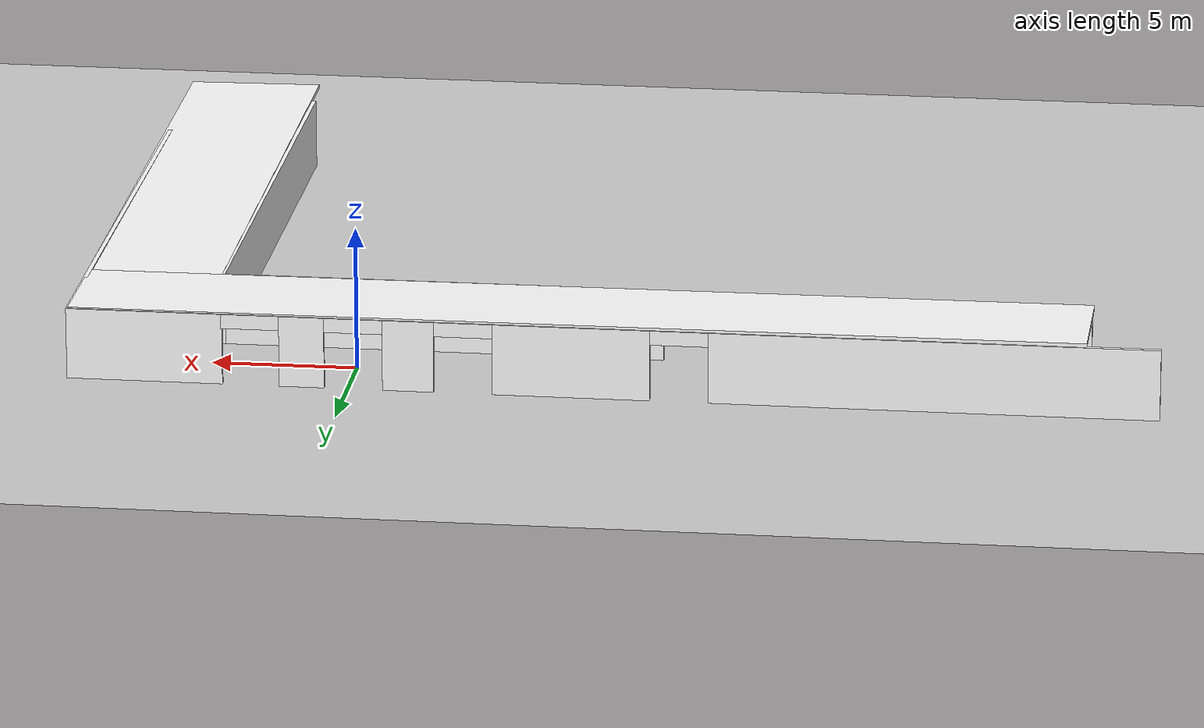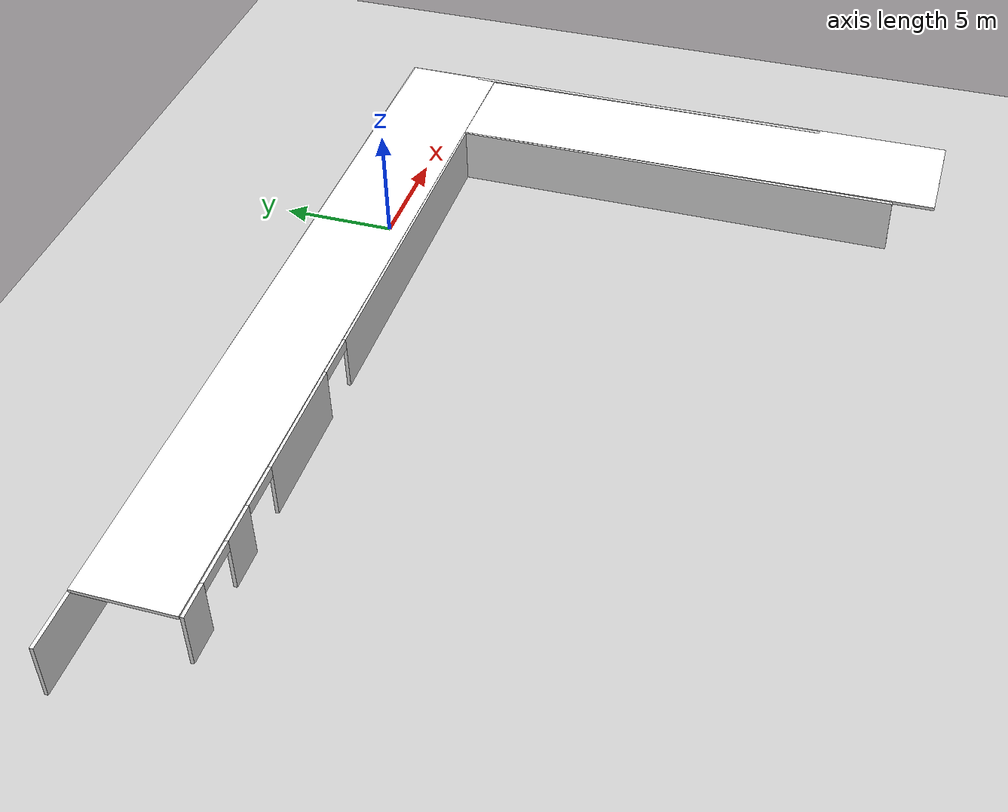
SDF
<sdf version="1.6">
 <world name="default">
  <physics name="default_physics" default="0" type="ode">
   <ode>
    <solver>
     <type>quick</type>
     <iters>100</iters>
     <sor>1</sor>
     <use_dynamic_moi_rescaling>0</use_dynamic_moi_rescaling>
    </solver>
    <constraints>
     <cfm>0</cfm>
     <erp>0.2</erp>
     <contact_max_correcting_vel>1000</contact_max_correcting_vel>
     <contact_surface_layer>0</contact_surface_layer>
    </constraints>
   </ode>
   <real_time_update_rate>1000</real_time_update_rate>
   <max_step_size>0.001</max_step_size>
   <real_time_factor>1</real_time_factor>
  </physics>
  <gravity>0 0 -9.8</gravity>
  <light name="sun" type="directional">
   <pose>0 0 10 0 -0 0</pose>
   <diffuse>0.8 0.8 0.8 1</diffuse>
   <specular>0.2 0.2 0.2 1</specular>
   <attenuation>
    <range>1000</range>
    <constant>0.9</constant>
    <linear>0.01</linear>
    <quadratic>0.001</quadratic>
   </attenuation>
   <direction>-0.5 0.1 -0.9</direction>
  </light>
  <model name="ground_plane">
   <static>1</static>
   <link name="link">
    <collision name="collision">
     <geometry><plane><normal>0 0 1</normal><size>5000 5000</size></plane></geometry>
     <surface><friction><ode><mu>1</mu><mu2>2</mu2></ode></friction></surface>
    </collision>
    <visual name="runway">
     <cast_shadows>0</cast_shadows>
     <geometry><plane><normal>0 0 1</normal><size>700 700</size></plane></geometry>
     <material>
      <script><uri>file://media/materials/scripts/gazebo.material</uri><name>Gazebo/Gray</name></script>
     </material>
    </visual>
   </link>
  </model>
  <magnetic_field>6e-06 2.3e-05 -4.2e-05</magnetic_field>
  <atmosphere type="adiabatic"/>
  <scene><ambient>0.4 0.4 0.4 1</ambient><background>0.7 0.7 0.7 1</background><shadows>1</shadows></scene>
  <audio><device>default</device></audio>
  <spherical_coordinates>
   <surface_model>EARTH_WGS84</surface_model>
   <latitude_deg>0</latitude_deg>
   <longitude_deg>0</longitude_deg>
   <elevation>0</elevation>
   <heading_deg>0</heading_deg>
  </spherical_coordinates>
  <model name="wall_with_door_0">
   <link name="Wall_2">
    <inertial>
     <inertia><ixx>0</ixx><ixy>0</ixy><ixz>0</ixz><iyy>0</iyy><iyz>0</iyz><izz>0</izz></inertia>
     <mass>0</mass>
    </inertial>
    <visual name="Wall_2_Visual_4">
     <pose>2.1425 0 1.25 0 -0 0</pose>
     <geometry><box><size>20.0858 0.15 2.5</size></box></geometry>
     <material>
      <script>
       <uri>model://floor/materials/scripts</uri>
       <uri>model://floor/materials/textures</uri>
       <name>floor</name>
      </script>
      <ambient>1 1 1 1</ambient>
      <shader type="vertex"><normal_map>__default__</normal_map></shader>
     </material>
     <meta><layer>0</layer></meta>
    </visual>
    <collision name="Wall_2_Collision_8">
     <pose>45.239 0 1.25 0 -0 0</pose>
     <geometry><box><size>0.462241 0.15 2.5</size></box></geometry>
     <surface>
      <friction>
       <ode><mu>1</mu><mu2>1</mu2><fdir1>0 0 0</fdir1><slip1>0</slip1><slip2>0</slip2></ode>
       <torsional>
        <coefficient>1</coefficient>
        <patch_radius>0</patch_radius>
        <surface_radius>0</surface_radius>
        <use_patch_radius>1</use_patch_radius>
        <ode><slip>0</slip></ode>
       </torsional>
      </friction>
      <bounce><restitution_coefficient>0</restitution_coefficient><threshold>1e+06</threshold></bounce>
      <contact>
       <collide_without_contact>0</collide_without_contact>
       <collide_without_contact_bitmask>1</collide_without_contact_bitmask>
       <collide_bitmask>1</collide_bitmask>
       <ode>
        <soft_cfm>0</soft_cfm>
        <soft_erp>0.2</soft_erp>
        <kp>1e+13</kp>
        <kd>1</kd>
        <max_vel>0.01</max_vel>
        <min_depth>0</min_depth>
       </ode>
       <bullet>
        <split_impulse>1</split_impulse>
        <split_impulse_penetration_threshold>-0.01</split_impulse_penetration_threshold>
        <soft_cfm>0</soft_cfm>
        <soft_erp>0.2</soft_erp>
        <kp>1e+13</kp>
        <kd>1</kd>
       </bullet>
      </contact>
     </surface>
    </collision>
    <collision name="Wall_2_Collision_9">
     <pose>50.4005 0 1.25 0 -0 0</pose>
     <geometry><box><size>2.68417 0.15 2.5</size></box></geometry>
     <surface>
      <friction>
       <ode><mu>1</mu><mu2>1</mu2><fdir1>0 0 0</fdir1><slip1>0</slip1><slip2>0</slip2></ode>
       <torsional>
        <coefficient>1</coefficient>
        <patch_radius>0</patch_radius>
        <surface_radius>0</surface_radius>
        <use_patch_radius>1</use_patch_radius>
        <ode><slip>0</slip></ode>
       </torsional>
      </friction>
      <bounce><restitution_coefficient>0</restitution_coefficient><threshold>1e+06</threshold></bounce>
      <contact>
       <collide_without_contact>0</collide_without_contact>
       <collide_without_contact_bitmask>1</collide_without_contact_bitmask>
       <collide_bitmask>1</collide_bitmask>
       <ode>
        <soft_cfm>0</soft_cfm>
        <soft_erp>0.2</soft_erp>
        <kp>1e+13</kp>
        <kd>1</kd>
        <max_vel>0.01</max_vel>
        <min_depth>0</min_depth>
       </ode>
       <bullet>
        <split_impulse>1</split_impulse>
        <split_impulse_penetration_threshold>-0.01</split_impulse_penetration_threshold>
        <soft_cfm>0</soft_cfm>
        <soft_erp>0.2</soft_erp>
        <kp>1e+13</kp>
        <kd>1</kd>
       </bullet>
      </contact>
     </surface>
    </collision>
    <collision name="Door_2_Collision_1">
     <pose>-26.352 0 2.25 0 -0 0</pose>
     <geometry><box><size>0.995439 0.15 0.5</size></box></geometry>
     <surface>
      <friction>
       <ode><mu>1</mu><mu2>1</mu2><fdir1>0 0 0</fdir1><slip1>0</slip1><slip2>0</slip2></ode>
       <torsional>
        <coefficient>1</coefficient>
        <patch_radius>0</patch_radius>
        <surface_radius>0</surface_radius>
        <use_patch_radius>1</use_patch_radius>
        <ode><slip>0</slip></ode>
       </torsional>
      </friction>
      <bounce><restitution_coefficient>0</restitution_coefficient><threshold>1e+06</threshold></bounce>
      <contact>
       <collide_without_contact>0</collide_without_contact>
       <collide_without_contact_bitmask>1</collide_without_contact_bitmask>
       <collide_bitmask>1</collide_bitmask>
       <ode>
        <soft_cfm>0</soft_cfm>
        <soft_erp>0.2</soft_erp>
        <kp>1e+13</kp>
        <kd>1</kd>
        <max_vel>0.01</max_vel>
        <min_depth>0</min_depth>
       </ode>
       <bullet>
        <split_impulse>1</split_impulse>
        <split_impulse_penetration_threshold>-0.01</split_impulse_penetration_threshold>
        <soft_cfm>0</soft_cfm>
        <soft_erp>0.2</soft_erp>
        <kp>1e+13</kp>
        <kd>1</kd>
       </bullet>
      </contact>
     </surface>
    </collision>
    <collision name="Door_2_Collision_0">
     <pose>-33.729 0 2.25 0 -0 0</pose>
     <geometry><box><size>0.995439 0.15 0.5</size></box></geometry>
     <surface>
      <friction>
       <ode><mu>1</mu><mu2>1</mu2><fdir1>0 0 0</fdir1><slip1>0</slip1><slip2>0</slip2></ode>
       <torsional>
        <coefficient>1</coefficient>
        <patch_radius>0</patch_radius>
        <surface_radius>0</surface_radius>
        <use_patch_radius>1</use_patch_radius>
        <ode><slip>0</slip></ode>
       </torsional>
      </friction>
      <bounce><restitution_coefficient>0</restitution_coefficient><threshold>1e+06</threshold></bounce>
      <contact>
       <collide_without_contact>0</collide_without_contact>
       <collide_without_contact_bitmask>1</collide_without_contact_bitmask>
       <collide_bitmask>1</collide_bitmask>
       <ode>
        <soft_cfm>0</soft_cfm>
        <soft_erp>0.2</soft_erp>
        <kp>1e+13</kp>
        <kd>1</kd>
        <max_vel>0.01</max_vel>
        <min_depth>0</min_depth>
       </ode>
       <bullet>
        <split_impulse>1</split_impulse>
        <split_impulse_penetration_threshold>-0.01</split_impulse_penetration_threshold>
        <soft_cfm>0</soft_cfm>
        <soft_erp>0.2</soft_erp>
        <kp>1e+13</kp>
        <kd>1</kd>
       </bullet>
      </contact>
     </surface>
    </collision>
    <collision name="Door_2_Collision_2">
     <pose>-22.592 0 2.25 0 -0 0</pose>
     <geometry><box><size>0.995439 0.15 0.5</size></box></geometry>
     <surface>
      <friction>
       <ode><mu>1</mu><mu2>1</mu2><fdir1>0 0 0</fdir1><slip1>0</slip1><slip2>0</slip2></ode>
       <torsional>
        <coefficient>1</coefficient>
        <patch_radius>0</patch_radius>
        <surface_radius>0</surface_radius>
        <use_patch_radius>1</use_patch_radius>
        <ode><slip>0</slip></ode>
       </torsional>
      </friction>
      <bounce><restitution_coefficient>0</restitution_coefficient><threshold>1e+06</threshold></bounce>
      <contact>
       <collide_without_contact>0</collide_without_contact>
       <collide_without_contact_bitmask>1</collide_without_contact_bitmask>
       <collide_bitmask>1</collide_bitmask>
       <ode>
        <soft_cfm>0</soft_cfm>
        <soft_erp>0.2</soft_erp>
        <kp>1e+13</kp>
        <kd>1</kd>
        <max_vel>0.01</max_vel>
        <min_depth>0</min_depth>
       </ode>
       <bullet>
        <split_impulse>1</split_impulse>
        <split_impulse_penetration_threshold>-0.01</split_impulse_penetration_threshold>
        <soft_cfm>0</soft_cfm>
        <soft_erp>0.2</soft_erp>
        <kp>1e+13</kp>
        <kd>1</kd>
       </bullet>
      </contact>
     </surface>
    </collision>
    <collision name="Door_2_Collision_3">
     <pose>-19.043 0 2.25 0 -0 0</pose>
     <geometry><box><size>0.995439 0.15 0.5</size></box></geometry>
     <surface>
      <friction>
       <ode><mu>1</mu><mu2>1</mu2><fdir1>0 0 0</fdir1><slip1>0</slip1><slip2>0</slip2></ode>
       <torsional>
        <coefficient>1</coefficient>
        <patch_radius>0</patch_radius>
        <surface_radius>0</surface_radius>
        <use_patch_radius>1</use_patch_radius>
        <ode><slip>0</slip></ode>
       </torsional>
      </friction>
      <bounce><restitution_coefficient>0</restitution_coefficient><threshold>1e+06</threshold></bounce>
      <contact>
       <collide_without_contact>0</collide_without_contact>
       <collide_without_contact_bitmask>1</collide_without_contact_bitmask>
       <collide_bitmask>1</collide_bitmask>
       <ode>
        <soft_cfm>0</soft_cfm>
        <soft_erp>0.2</soft_erp>
        <kp>1e+13</kp>
        <kd>1</kd>
        <max_vel>0.01</max_vel>
        <min_depth>0</min_depth>
       </ode>
       <bullet>
        <split_impulse>1</split_impulse>
        <split_impulse_penetration_threshold>-0.01</split_impulse_penetration_threshold>
        <soft_cfm>0</soft_cfm>
        <soft_erp>0.2</soft_erp>
        <kp>1e+13</kp>
        <kd>1</kd>
       </bullet>
      </contact>
     </surface>
    </collision>
    <collision name="Door_2_Collision_4">
     <pose>23.328 0 2.25 0 -0 0</pose>
     <geometry><box><size>0.995439 0.15 0.5</size></box></geometry>
     <surface>
      <friction>
       <ode><mu>1</mu><mu2>1</mu2><fdir1>0 0 0</fdir1><slip1>0</slip1><slip2>0</slip2></ode>
       <torsional>
        <coefficient>1</coefficient>
        <patch_radius>0</patch_radius>
        <surface_radius>0</surface_radius>
        <use_patch_radius>1</use_patch_radius>
        <ode><slip>0</slip></ode>
       </torsional>
      </friction>
      <bounce><restitution_coefficient>0</restitution_coefficient><threshold>1e+06</threshold></bounce>
      <contact>
       <collide_without_contact>0</collide_without_contact>
       <collide_without_contact_bitmask>1</collide_without_contact_bitmask>
       <collide_bitmask>1</collide_bitmask>
       <ode>
        <soft_cfm>0</soft_cfm>
        <soft_erp>0.2</soft_erp>
        <kp>1e+13</kp>
        <kd>1</kd>
        <max_vel>0.01</max_vel>
        <min_depth>0</min_depth>
       </ode>
       <bullet>
        <split_impulse>1</split_impulse>
        <split_impulse_penetration_threshold>-0.01</split_impulse_penetration_threshold>
        <soft_cfm>0</soft_cfm>
        <soft_erp>0.2</soft_erp>
        <kp>1e+13</kp>
        <kd>1</kd>
       </bullet>
      </contact>
     </surface>
    </collision>
    <collision name="Wall_2_Collision_4">
     <pose>2.1425 0 1.25 0 -0 0</pose>
     <geometry><box><size>20.0858 0.15 2.5</size></box></geometry>
     <surface>
      <friction>
       <ode><mu>1</mu><mu2>1</mu2><fdir1>0 0 0</fdir1><slip1>0</slip1><slip2>0</slip2></ode>
       <torsional>
        <coefficient>1</coefficient>
        <patch_radius>0</patch_radius>
        <surface_radius>0</surface_radius>
        <use_patch_radius>1</use_patch_radius>
        <ode><slip>0</slip></ode>
       </torsional>
      </friction>
      <bounce><restitution_coefficient>0</restitution_coefficient><threshold>1e+06</threshold></bounce>
      <contact>
       <collide_without_contact>0</collide_without_contact>
       <collide_without_contact_bitmask>1</collide_without_contact_bitmask>
       <collide_bitmask>1</collide_bitmask>
       <ode>
        <soft_cfm>0</soft_cfm>
        <soft_erp>0.2</soft_erp>
        <kp>1e+13</kp>
        <kd>1</kd>
        <max_vel>0.01</max_vel>
        <min_depth>0</min_depth>
       </ode>
       <bullet>
        <split_impulse>1</split_impulse>
        <split_impulse_penetration_threshold>-0.01</split_impulse_penetration_threshold>
        <soft_cfm>0</soft_cfm>
        <soft_erp>0.2</soft_erp>
        <kp>1e+13</kp>
        <kd>1</kd>
       </bullet>
      </contact>
     </surface>
    </collision>
    <collision name="Wall_2_Collision_5">
     <pose>26.519 0 1.25 0 -0 0</pose>
     <geometry><box><size>2.18101 0.15 2.5</size></box></geometry>
     <surface>
      <friction>
       <ode><mu>1</mu><mu2>1</mu2><fdir1>0 0 0</fdir1><slip1>0</slip1><slip2>0</slip2></ode>
       <torsional>
        <coefficient>1</coefficient>
        <patch_radius>0</patch_radius>
        <surface_radius>0</surface_radius>
        <use_patch_radius>1</use_patch_radius>
        <ode><slip>0</slip></ode>
       </torsional>
      </friction>
      <bounce><restitution_coefficient>0</restitution_coefficient><threshold>1e+06</threshold></bounce>
      <contact>
       <collide_without_contact>0</collide_without_contact>
       <collide_without_contact_bitmask>1</collide_without_contact_bitmask>
       <collide_bitmask>1</collide_bitmask>
       <ode>
        <soft_cfm>0</soft_cfm>
        <soft_erp>0.2</soft_erp>
        <kp>1e+13</kp>
        <kd>1</kd>
        <max_vel>0.01</max_vel>
        <min_depth>0</min_depth>
       </ode>
       <bullet>
        <split_impulse>1</split_impulse>
        <split_impulse_penetration_threshold>-0.01</split_impulse_penetration_threshold>
        <soft_cfm>0</soft_cfm>
        <soft_erp>0.2</soft_erp>
        <kp>1e+13</kp>
        <kd>1</kd>
       </bullet>
      </contact>
     </surface>
    </collision>
    <collision name="Wall_2_Collision_6">
     <pose>35.369 0 1.25 0 -0 0</pose>
     <geometry><box><size>4.63597 0.15 2.5</size></box></geometry>
     <surface>
      <friction>
       <ode><mu>1</mu><mu2>1</mu2><fdir1>0 0 0</fdir1><slip1>0</slip1><slip2>0</slip2></ode>
       <torsional>
        <coefficient>1</coefficient>
        <patch_radius>0</patch_radius>
        <surface_radius>0</surface_radius>
        <use_patch_radius>1</use_patch_radius>
        <ode><slip>0</slip></ode>
       </torsional>
      </friction>
      <bounce><restitution_coefficient>0</restitution_coefficient><threshold>1e+06</threshold></bounce>
      <contact>
       <collide_without_contact>0</collide_without_contact>
       <collide_without_contact_bitmask>1</collide_without_contact_bitmask>
       <collide_bitmask>1</collide_bitmask>
       <ode>
        <soft_cfm>0</soft_cfm>
        <soft_erp>0.2</soft_erp>
        <kp>1e+13</kp>
        <kd>1</kd>
        <max_vel>0.01</max_vel>
        <min_depth>0</min_depth>
       </ode>
       <bullet>
        <split_impulse>1</split_impulse>
        <split_impulse_penetration_threshold>-0.01</split_impulse_penetration_threshold>
        <soft_cfm>0</soft_cfm>
        <soft_erp>0.2</soft_erp>
        <kp>1e+13</kp>
        <kd>1</kd>
       </bullet>
      </contact>
     </surface>
    </collision>
    <collision name="Wall_2_Collision_7">
     <pose>42.4015 0 1.25 0 -0 0</pose>
     <geometry><box><size>0.372084 0.15 2.5</size></box></geometry>
     <surface>
      <friction>
       <ode><mu>1</mu><mu2>1</mu2><fdir1>0 0 0</fdir1><slip1>0</slip1><slip2>0</slip2></ode>
       <torsional>
        <coefficient>1</coefficient>
        <patch_radius>0</patch_radius>
        <surface_radius>0</surface_radius>
        <use_patch_radius>1</use_patch_radius>
        <ode><slip>0</slip></ode>
       </torsional>
      </friction>
      <bounce><restitution_coefficient>0</restitution_coefficient><threshold>1e+06</threshold></bounce>
      <contact>
       <collide_without_contact>0</collide_without_contact>
       <collide_without_contact_bitmask>1</collide_without_contact_bitmask>
       <collide_bitmask>1</collide_bitmask>
       <ode>
        <soft_cfm>0</soft_cfm>
        <soft_erp>0.2</soft_erp>
        <kp>1e+13</kp>
        <kd>1</kd>
        <max_vel>0.01</max_vel>
        <min_depth>0</min_depth>
       </ode>
       <bullet>
        <split_impulse>1</split_impulse>
        <split_impulse_penetration_threshold>-0.01</split_impulse_penetration_threshold>
        <soft_cfm>0</soft_cfm>
        <soft_erp>0.2</soft_erp>
        <kp>1e+13</kp>
        <kd>1</kd>
       </bullet>
      </contact>
     </surface>
    </collision>
    <collision name="Wall_2_Collision_0">
     <pose>-42.3645 0 1.25 0 -0 0</pose>
     <geometry><box><size>7.59777 0.15 2.5</size></box></geometry>
     <surface>
      <friction>
       <ode><mu>1</mu><mu2>1</mu2><fdir1>0 0 0</fdir1><slip1>0</slip1><slip2>0</slip2></ode>
       <torsional>
        <coefficient>1</coefficient>
        <patch_radius>0</patch_radius>
        <surface_radius>0</surface_radius>
        <use_patch_radius>1</use_patch_radius>
        <ode><slip>0</slip></ode>
       </torsional>
      </friction>
      <bounce><restitution_coefficient>0</restitution_coefficient><threshold>1e+06</threshold></bounce>
      <contact>
       <collide_without_contact>0</collide_without_contact>
       <collide_without_contact_bitmask>1</collide_without_contact_bitmask>
       <collide_bitmask>1</collide_bitmask>
       <ode>
        <soft_cfm>0</soft_cfm>
        <soft_erp>0.2</soft_erp>
        <kp>1e+13</kp>
        <kd>1</kd>
        <max_vel>0.01</max_vel>
        <min_depth>0</min_depth>
       </ode>
       <bullet>
        <split_impulse>1</split_impulse>
        <split_impulse_penetration_threshold>-0.01</split_impulse_penetration_threshold>
        <soft_cfm>0</soft_cfm>
        <soft_erp>0.2</soft_erp>
        <kp>1e+13</kp>
        <kd>1</kd>
       </bullet>
      </contact>
     </surface>
    </collision>
    <collision name="Wall_2_Collision_1">
     <pose>-30.0405 0 1.25 0 -0 0</pose>
     <geometry><box><size>2.67522 0.15 2.5</size></box></geometry>
     <surface>
      <friction>
       <ode><mu>1</mu><mu2>1</mu2><fdir1>0 0 0</fdir1><slip1>0</slip1><slip2>0</slip2></ode>
       <torsional>
        <coefficient>1</coefficient>
        <patch_radius>0</patch_radius>
        <surface_radius>0</surface_radius>
        <use_patch_radius>1</use_patch_radius>
        <ode><slip>0</slip></ode>
       </torsional>
      </friction>
      <bounce><restitution_coefficient>0</restitution_coefficient><threshold>1e+06</threshold></bounce>
      <contact>
       <collide_without_contact>0</collide_without_contact>
       <collide_without_contact_bitmask>1</collide_without_contact_bitmask>
       <collide_bitmask>1</collide_bitmask>
       <ode>
        <soft_cfm>0</soft_cfm>
        <soft_erp>0.2</soft_erp>
        <kp>1e+13</kp>
        <kd>1</kd>
        <max_vel>0.01</max_vel>
        <min_depth>0</min_depth>
       </ode>
       <bullet>
        <split_impulse>1</split_impulse>
        <split_impulse_penetration_threshold>-0.01</split_impulse_penetration_threshold>
        <soft_cfm>0</soft_cfm>
        <soft_erp>0.2</soft_erp>
        <kp>1e+13</kp>
        <kd>1</kd>
       </bullet>
      </contact>
     </surface>
    </collision>
    <collision name="Wall_2_Collision_3">
     <pose>-20.8175 0 1.25 0 -0 0</pose>
     <geometry><box><size>0.771564 0.15 2.5</size></box></geometry>
     <surface>
      <friction>
       <ode><mu>1</mu><mu2>1</mu2><fdir1>0 0 0</fdir1><slip1>0</slip1><slip2>0</slip2></ode>
       <torsional>
        <coefficient>1</coefficient>
        <patch_radius>0</patch_radius>
        <surface_radius>0</surface_radius>
        <use_patch_radius>1</use_patch_radius>
        <ode><slip>0</slip></ode>
       </torsional>
      </friction>
      <bounce><restitution_coefficient>0</restitution_coefficient><threshold>1e+06</threshold></bounce>
      <contact>
       <collide_without_contact>0</collide_without_contact>
       <collide_without_contact_bitmask>1</collide_without_contact_bitmask>
       <collide_bitmask>1</collide_bitmask>
       <ode>
        <soft_cfm>0</soft_cfm>
        <soft_erp>0.2</soft_erp>
        <kp>1e+13</kp>
        <kd>1</kd>
        <max_vel>0.01</max_vel>
        <min_depth>0</min_depth>
       </ode>
       <bullet>
        <split_impulse>1</split_impulse>
        <split_impulse_penetration_threshold>-0.01</split_impulse_penetration_threshold>
        <soft_cfm>0</soft_cfm>
        <soft_erp>0.2</soft_erp>
        <kp>1e+13</kp>
        <kd>1</kd>
       </bullet>
      </contact>
     </surface>
    </collision>
    <collision name="Wall_2_Collision_2">
     <pose>-24.472 0 1.25 0 -0 0</pose>
     <geometry><box><size>0.876664 0.15 2.5</size></box></geometry>
     <surface>
      <friction>
       <ode><mu>1</mu><mu2>1</mu2><fdir1>0 0 0</fdir1><slip1>0</slip1><slip2>0</slip2></ode>
       <torsional>
        <coefficient>1</coefficient>
        <patch_radius>0</patch_radius>
        <surface_radius>0</surface_radius>
        <use_patch_radius>1</use_patch_radius>
        <ode><slip>0</slip></ode>
       </torsional>
      </friction>
      <bounce><restitution_coefficient>0</restitution_coefficient><threshold>1e+06</threshold></bounce>
      <contact>
       <collide_without_contact>0</collide_without_contact>
       <collide_without_contact_bitmask>1</collide_without_contact_bitmask>
       <collide_bitmask>1</collide_bitmask>
       <ode>
        <soft_cfm>0</soft_cfm>
        <soft_erp>0.2</soft_erp>
        <kp>1e+13</kp>
        <kd>1</kd>
        <max_vel>0.01</max_vel>
        <min_depth>0</min_depth>
       </ode>
       <bullet>
        <split_impulse>1</split_impulse>
        <split_impulse_penetration_threshold>-0.01</split_impulse_penetration_threshold>
        <soft_cfm>0</soft_cfm>
        <soft_erp>0.2</soft_erp>
        <kp>1e+13</kp>
        <kd>1</kd>
       </bullet>
      </contact>
     </surface>
    </collision>
    <collision name="Door_2_Collision_5">
     <pose>29.71 0 2.25 0 -0 0</pose>
     <geometry><box><size>0.995439 0.15 0.5</size></box></geometry>
     <surface>
      <friction>
       <ode><mu>1</mu><mu2>1</mu2><fdir1>0 0 0</fdir1><slip1>0</slip1><slip2>0</slip2></ode>
       <torsional>
        <coefficient>1</coefficient>
        <patch_radius>0</patch_radius>
        <surface_radius>0</surface_radius>
        <use_patch_radius>1</use_patch_radius>
        <ode><slip>0</slip></ode>
       </torsional>
      </friction>
      <bounce><restitution_coefficient>0</restitution_coefficient><threshold>1e+06</threshold></bounce>
      <contact>
       <collide_without_contact>0</collide_without_contact>
       <collide_without_contact_bitmask>1</collide_without_contact_bitmask>
       <collide_bitmask>1</collide_bitmask>
       <ode>
        <soft_cfm>0</soft_cfm>
        <soft_erp>0.2</soft_erp>
        <kp>1e+13</kp>
        <kd>1</kd>
        <max_vel>0.01</max_vel>
        <min_depth>0</min_depth>
       </ode>
       <bullet>
        <split_impulse>1</split_impulse>
        <split_impulse_penetration_threshold>-0.01</split_impulse_penetration_threshold>
        <soft_cfm>0</soft_cfm>
        <soft_erp>0.2</soft_erp>
        <kp>1e+13</kp>
        <kd>1</kd>
       </bullet>
      </contact>
     </surface>
    </collision>
    <collision name="Door_2_Collision_6">
     <pose>41.028 0 2.25 0 -0 0</pose>
     <geometry><box><size>0.995439 0.15 0.5</size></box></geometry>
     <surface>
      <friction>
       <ode><mu>1</mu><mu2>1</mu2><fdir1>0 0 0</fdir1><slip1>0</slip1><slip2>0</slip2></ode>
       <torsional>
        <coefficient>1</coefficient>
        <patch_radius>0</patch_radius>
        <surface_radius>0</surface_radius>
        <use_patch_radius>1</use_patch_radius>
        <ode><slip>0</slip></ode>
       </torsional>
      </friction>
      <bounce><restitution_coefficient>0</restitution_coefficient><threshold>1e+06</threshold></bounce>
      <contact>
       <collide_without_contact>0</collide_without_contact>
       <collide_without_contact_bitmask>1</collide_without_contact_bitmask>
       <collide_bitmask>1</collide_bitmask>
       <ode>
        <soft_cfm>0</soft_cfm>
        <soft_erp>0.2</soft_erp>
        <kp>1e+13</kp>
        <kd>1</kd>
        <max_vel>0.01</max_vel>
        <min_depth>0</min_depth>
       </ode>
       <bullet>
        <split_impulse>1</split_impulse>
        <split_impulse_penetration_threshold>-0.01</split_impulse_penetration_threshold>
        <soft_cfm>0</soft_cfm>
        <soft_erp>0.2</soft_erp>
        <kp>1e+13</kp>
        <kd>1</kd>
       </bullet>
      </contact>
     </surface>
    </collision>
    <collision name="Door_2_Collision_8">
     <pose>46.703 0 2.25 0 -0 0</pose>
     <geometry><box><size>0.995439 0.15 0.5</size></box></geometry>
     <surface>
      <friction>
       <ode><mu>1</mu><mu2>1</mu2><fdir1>0 0 0</fdir1><slip1>0</slip1><slip2>0</slip2></ode>
       <torsional>
        <coefficient>1</coefficient>
        <patch_radius>0</patch_radius>
        <surface_radius>0</surface_radius>
        <use_patch_radius>1</use_patch_radius>
        <ode><slip>0</slip></ode>
       </torsional>
      </friction>
      <bounce><restitution_coefficient>0</restitution_coefficient><threshold>1e+06</threshold></bounce>
      <contact>
       <collide_without_contact>0</collide_without_contact>
       <collide_without_contact_bitmask>1</collide_without_contact_bitmask>
       <collide_bitmask>1</collide_bitmask>
       <ode>
        <soft_cfm>0</soft_cfm>
        <soft_erp>0.2</soft_erp>
        <kp>1e+13</kp>
        <kd>1</kd>
        <max_vel>0.01</max_vel>
        <min_depth>0</min_depth>
       </ode>
       <bullet>
        <split_impulse>1</split_impulse>
        <split_impulse_penetration_threshold>-0.01</split_impulse_penetration_threshold>
        <soft_cfm>0</soft_cfm>
        <soft_erp>0.2</soft_erp>
        <kp>1e+13</kp>
        <kd>1</kd>
       </bullet>
      </contact>
     </surface>
    </collision>
    <collision name="Door_2_Collision_7">
     <pose>43.775 0 2.25 0 -0 0</pose>
     <geometry><box><size>0.995439 0.15 0.5</size></box></geometry>
     <surface>
      <friction>
       <ode><mu>1</mu><mu2>1</mu2><fdir1>0 0 0</fdir1><slip1>0</slip1><slip2>0</slip2></ode>
       <torsional>
        <coefficient>1</coefficient>
        <patch_radius>0</patch_radius>
        <surface_radius>0</surface_radius>
        <use_patch_radius>1</use_patch_radius>
        <ode><slip>0</slip></ode>
       </torsional>
      </friction>
      <bounce><restitution_coefficient>0</restitution_coefficient><threshold>1e+06</threshold></bounce>
      <contact>
       <collide_without_contact>0</collide_without_contact>
       <collide_without_contact_bitmask>1</collide_without_contact_bitmask>
       <collide_bitmask>1</collide_bitmask>
       <ode>
        <soft_cfm>0</soft_cfm>
        <soft_erp>0.2</soft_erp>
        <kp>1e+13</kp>
        <kd>1</kd>
        <max_vel>0.01</max_vel>
        <min_depth>0</min_depth>
       </ode>
       <bullet>
        <split_impulse>1</split_impulse>
        <split_impulse_penetration_threshold>-0.01</split_impulse_penetration_threshold>
        <soft_cfm>0</soft_cfm>
        <soft_erp>0.2</soft_erp>
        <kp>1e+13</kp>
        <kd>1</kd>
       </bullet>
      </contact>
     </surface>
    </collision>
   </link>
   <static>1</static>
   <pose>9.5837 -5.89513 0 0 0 -1.57544</pose>
  </model>
  <model name="wall_with_door_short">
   <link name="Wall_2">
    <inertial>
     <mass>1</mass>
     <inertia><ixx>1</ixx><ixy>0</ixy><ixz>0</ixz><iyy>1</iyy><iyz>0</iyz><izz>1</izz></inertia>
    </inertial>
    <visual name="Door_2_Visual_0">
     <pose>-33.729 0 2.25 0 -0 0</pose>
     <geometry><box><size>2 0.15 0.5</size></box></geometry>
     <material>
      <script>
       <uri>model://floor/materials/scripts</uri>
       <uri>model://floor/materials/textures</uri>
       <name>floor</name>
      </script>
      <ambient>1 1 1 1</ambient>
      <shader type="vertex"><normal_map>__default__</normal_map></shader>
     </material>
     <meta><layer>0</layer></meta>
    </visual>
    <visual name="Wall_2_Visual_0">
     <pose>-42.3645 0 1.25 0 -0 0</pose>
     <geometry><box><size>15.271 0.15 2.5</size></box></geometry>
     <material>
      <script>
       <uri>model://floor/materials/scripts</uri>
       <uri>model://floor/materials/textures</uri>
       <name>floor</name>
      </script>
      <ambient>1 1 1 1</ambient>
      <shader type="vertex"><normal_map>__default__</normal_map></shader>
     </material>
     <meta><layer>0</layer></meta>
    </visual>
    <visual name="Wall_2_Visual_1">
     <pose>-30.0405 0 1.25 0 -0 0</pose>
     <geometry><box><size>5.377 0.15 2.5</size></box></geometry>
     <material>
      <script>
       <uri>model://floor/materials/scripts</uri>
       <uri>model://floor/materials/textures</uri>
       <name>floor</name>
      </script>
      <ambient>1 1 1 1</ambient>
      <shader type="vertex"><normal_map>__default__</normal_map></shader>
     </material>
     <meta><layer>0</layer></meta>
    </visual>
    <visual name="Door_2_Visual_2">
     <pose>-22.592 0 2.25 0 -0 0</pose>
     <geometry><box><size>2 0.15 0.5</size></box></geometry>
     <material>
      <script>
       <uri>model://floor/materials/scripts</uri>
       <uri>model://floor/materials/textures</uri>
       <name>floor</name>
      </script>
      <ambient>1 1 1 1</ambient>
      <shader type="vertex"><normal_map>__default__</normal_map></shader>
     </material>
     <meta><layer>0</layer></meta>
    </visual>
    <visual name="Door_2_Visual_1">
     <pose>-26.352 0 2.25 0 -0 0</pose>
     <geometry><box><size>2 0.15 0.5</size></box></geometry>
     <material>
      <script>
       <uri>model://floor/materials/scripts</uri>
       <uri>model://floor/materials/textures</uri>
       <name>floor</name>
      </script>
      <ambient>1 1 1 1</ambient>
      <shader type="vertex"><normal_map>__default__</normal_map></shader>
     </material>
     <meta><layer>0</layer></meta>
    </visual>
    <visual name="Wall_2_Visual_2">
     <pose>-24.472 0 1.25 0 -0 0</pose>
     <geometry><box><size>1.76 0.15 2.5</size></box></geometry>
     <material>
      <script>
       <uri>model://floor/materials/scripts</uri>
       <uri>model://floor/materials/textures</uri>
       <name>floor</name>
      </script>
      <ambient>1 1 1 1</ambient>
      <shader type="vertex"><normal_map>__default__</normal_map></shader>
     </material>
     <meta><layer>0</layer></meta>
    </visual>
    <visual name="Wall_2_Visual_3">
     <pose>-20.8175 0 1.25 0 -0 0</pose>
     <geometry><box><size>1.549 0.15 2.5</size></box></geometry>
     <material>
      <script>
       <uri>model://floor/materials/scripts</uri>
       <uri>model://floor/materials/textures</uri>
       <name>floor</name>
      </script>
      <ambient>1 1 1 1</ambient>
      <shader type="vertex"><normal_map>__default__</normal_map></shader>
     </material>
     <meta><layer>0</layer></meta>
    </visual>
    <collision name="Door_2_Collision_6">
     <pose>41.028 0 2.25 0 -0 0</pose>
     <geometry><box><size>2 0.15 0.5</size></box></geometry>
     <surface>
      <friction>
       <ode><mu>1</mu><mu2>1</mu2><fdir1>0 0 0</fdir1><slip1>0</slip1><slip2>0</slip2></ode>
       <torsional>
        <coefficient>1</coefficient>
        <patch_radius>0</patch_radius>
        <surface_radius>0</surface_radius>
        <use_patch_radius>1</use_patch_radius>
        <ode><slip>0</slip></ode>
       </torsional>
      </friction>
      <bounce><restitution_coefficient>0</restitution_coefficient><threshold>1e+06</threshold></bounce>
      <contact>
       <collide_without_contact>0</collide_without_contact>
       <collide_without_contact_bitmask>1</collide_without_contact_bitmask>
       <collide_bitmask>1</collide_bitmask>
       <ode>
        <soft_cfm>0</soft_cfm>
        <soft_erp>0.2</soft_erp>
        <kp>1e+13</kp>
        <kd>1</kd>
        <max_vel>0.01</max_vel>
        <min_depth>0</min_depth>
       </ode>
       <bullet>
        <split_impulse>1</split_impulse>
        <split_impulse_penetration_threshold>-0.01</split_impulse_penetration_threshold>
        <soft_cfm>0</soft_cfm>
        <soft_erp>0.2</soft_erp>
        <kp>1e+13</kp>
        <kd>1</kd>
       </bullet>
      </contact>
     </surface>
    </collision>
    <collision name="Door_2_Collision_8">
     <pose>46.703 0 2.25 0 -0 0</pose>
     <geometry><box><size>2 0.15 0.5</size></box></geometry>
     <surface>
      <friction>
       <ode><mu>1</mu><mu2>1</mu2><fdir1>0 0 0</fdir1><slip1>0</slip1><slip2>0</slip2></ode>
       <torsional>
        <coefficient>1</coefficient>
        <patch_radius>0</patch_radius>
        <surface_radius>0</surface_radius>
        <use_patch_radius>1</use_patch_radius>
        <ode><slip>0</slip></ode>
       </torsional>
      </friction>
      <bounce><restitution_coefficient>0</restitution_coefficient><threshold>1e+06</threshold></bounce>
      <contact>
       <collide_without_contact>0</collide_without_contact>
       <collide_without_contact_bitmask>1</collide_without_contact_bitmask>
       <collide_bitmask>1</collide_bitmask>
       <ode>
        <soft_cfm>0</soft_cfm>
        <soft_erp>0.2</soft_erp>
        <kp>1e+13</kp>
        <kd>1</kd>
        <max_vel>0.01</max_vel>
        <min_depth>0</min_depth>
       </ode>
       <bullet>
        <split_impulse>1</split_impulse>
        <split_impulse_penetration_threshold>-0.01</split_impulse_penetration_threshold>
        <soft_cfm>0</soft_cfm>
        <soft_erp>0.2</soft_erp>
        <kp>1e+13</kp>
        <kd>1</kd>
       </bullet>
      </contact>
     </surface>
    </collision>
    <collision name="Wall_2_Collision_4">
     <pose>2.1425 0 1.25 0 -0 0</pose>
     <geometry><box><size>40.371 0.15 2.5</size></box></geometry>
     <surface>
      <friction>
       <ode><mu>1</mu><mu2>1</mu2><fdir1>0 0 0</fdir1><slip1>0</slip1><slip2>0</slip2></ode>
       <torsional>
        <coefficient>1</coefficient>
        <patch_radius>0</patch_radius>
        <surface_radius>0</surface_radius>
        <use_patch_radius>1</use_patch_radius>
        <ode><slip>0</slip></ode>
       </torsional>
      </friction>
      <bounce><restitution_coefficient>0</restitution_coefficient><threshold>1e+06</threshold></bounce>
      <contact>
       <collide_without_contact>0</collide_without_contact>
       <collide_without_contact_bitmask>1</collide_without_contact_bitmask>
       <collide_bitmask>1</collide_bitmask>
       <ode>
        <soft_cfm>0</soft_cfm>
        <soft_erp>0.2</soft_erp>
        <kp>1e+13</kp>
        <kd>1</kd>
        <max_vel>0.01</max_vel>
        <min_depth>0</min_depth>
       </ode>
       <bullet>
        <split_impulse>1</split_impulse>
        <split_impulse_penetration_threshold>-0.01</split_impulse_penetration_threshold>
        <soft_cfm>0</soft_cfm>
        <soft_erp>0.2</soft_erp>
        <kp>1e+13</kp>
        <kd>1</kd>
       </bullet>
      </contact>
     </surface>
    </collision>
    <collision name="Wall_2_Collision_2">
     <pose>-24.472 0 1.25 0 -0 0</pose>
     <geometry><box><size>1.76 0.15 2.5</size></box></geometry>
     <surface>
      <friction>
       <ode><mu>1</mu><mu2>1</mu2><fdir1>0 0 0</fdir1><slip1>0</slip1><slip2>0</slip2></ode>
       <torsional>
        <coefficient>1</coefficient>
        <patch_radius>0</patch_radius>
        <surface_radius>0</surface_radius>
        <use_patch_radius>1</use_patch_radius>
        <ode><slip>0</slip></ode>
       </torsional>
      </friction>
      <bounce><restitution_coefficient>0</restitution_coefficient><threshold>1e+06</threshold></bounce>
      <contact>
       <collide_without_contact>0</collide_without_contact>
       <collide_without_contact_bitmask>1</collide_without_contact_bitmask>
       <collide_bitmask>1</collide_bitmask>
       <ode>
        <soft_cfm>0</soft_cfm>
        <soft_erp>0.2</soft_erp>
        <kp>1e+13</kp>
        <kd>1</kd>
        <max_vel>0.01</max_vel>
        <min_depth>0</min_depth>
       </ode>
       <bullet>
        <split_impulse>1</split_impulse>
        <split_impulse_penetration_threshold>-0.01</split_impulse_penetration_threshold>
        <soft_cfm>0</soft_cfm>
        <soft_erp>0.2</soft_erp>
        <kp>1e+13</kp>
        <kd>1</kd>
       </bullet>
      </contact>
     </surface>
    </collision>
    <collision name="Wall_2_Collision_5">
     <pose>26.519 0 1.25 0 -0 0</pose>
     <geometry><box><size>4.382 0.15 2.5</size></box></geometry>
     <surface>
      <friction>
       <ode><mu>1</mu><mu2>1</mu2><fdir1>0 0 0</fdir1><slip1>0</slip1><slip2>0</slip2></ode>
       <torsional>
        <coefficient>1</coefficient>
        <patch_radius>0</patch_radius>
        <surface_radius>0</surface_radius>
        <use_patch_radius>1</use_patch_radius>
        <ode><slip>0</slip></ode>
       </torsional>
      </friction>
      <bounce><restitution_coefficient>0</restitution_coefficient><threshold>1e+06</threshold></bounce>
      <contact>
       <collide_without_contact>0</collide_without_contact>
       <collide_without_contact_bitmask>1</collide_without_contact_bitmask>
       <collide_bitmask>1</collide_bitmask>
       <ode>
        <soft_cfm>0</soft_cfm>
        <soft_erp>0.2</soft_erp>
        <kp>1e+13</kp>
        <kd>1</kd>
        <max_vel>0.01</max_vel>
        <min_depth>0</min_depth>
       </ode>
       <bullet>
        <split_impulse>1</split_impulse>
        <split_impulse_penetration_threshold>-0.01</split_impulse_penetration_threshold>
        <soft_cfm>0</soft_cfm>
        <soft_erp>0.2</soft_erp>
        <kp>1e+13</kp>
        <kd>1</kd>
       </bullet>
      </contact>
     </surface>
    </collision>
    <collision name="Door_2_Collision_1">
     <pose>-26.352 0 2.25 0 -0 0</pose>
     <geometry><box><size>2 0.15 0.5</size></box></geometry>
     <surface>
      <friction>
       <ode><mu>1</mu><mu2>1</mu2><fdir1>0 0 0</fdir1><slip1>0</slip1><slip2>0</slip2></ode>
       <torsional>
        <coefficient>1</coefficient>
        <patch_radius>0</patch_radius>
        <surface_radius>0</surface_radius>
        <use_patch_radius>1</use_patch_radius>
        <ode><slip>0</slip></ode>
       </torsional>
      </friction>
      <bounce><restitution_coefficient>0</restitution_coefficient><threshold>1e+06</threshold></bounce>
      <contact>
       <collide_without_contact>0</collide_without_contact>
       <collide_without_contact_bitmask>1</collide_without_contact_bitmask>
       <collide_bitmask>1</collide_bitmask>
       <ode>
        <soft_cfm>0</soft_cfm>
        <soft_erp>0.2</soft_erp>
        <kp>1e+13</kp>
        <kd>1</kd>
        <max_vel>0.01</max_vel>
        <min_depth>0</min_depth>
       </ode>
       <bullet>
        <split_impulse>1</split_impulse>
        <split_impulse_penetration_threshold>-0.01</split_impulse_penetration_threshold>
        <soft_cfm>0</soft_cfm>
        <soft_erp>0.2</soft_erp>
        <kp>1e+13</kp>
        <kd>1</kd>
       </bullet>
      </contact>
     </surface>
    </collision>
    <collision name="Door_2_Collision_2">
     <pose>-22.592 0 2.25 0 -0 0</pose>
     <geometry><box><size>2 0.15 0.5</size></box></geometry>
     <surface>
      <friction>
       <ode><mu>1</mu><mu2>1</mu2><fdir1>0 0 0</fdir1><slip1>0</slip1><slip2>0</slip2></ode>
       <torsional>
        <coefficient>1</coefficient>
        <patch_radius>0</patch_radius>
        <surface_radius>0</surface_radius>
        <use_patch_radius>1</use_patch_radius>
        <ode><slip>0</slip></ode>
       </torsional>
      </friction>
      <bounce><restitution_coefficient>0</restitution_coefficient><threshold>1e+06</threshold></bounce>
      <contact>
       <collide_without_contact>0</collide_without_contact>
       <collide_without_contact_bitmask>1</collide_without_contact_bitmask>
       <collide_bitmask>1</collide_bitmask>
       <ode>
        <soft_cfm>0</soft_cfm>
        <soft_erp>0.2</soft_erp>
        <kp>1e+13</kp>
        <kd>1</kd>
        <max_vel>0.01</max_vel>
        <min_depth>0</min_depth>
       </ode>
       <bullet>
        <split_impulse>1</split_impulse>
        <split_impulse_penetration_threshold>-0.01</split_impulse_penetration_threshold>
        <soft_cfm>0</soft_cfm>
        <soft_erp>0.2</soft_erp>
        <kp>1e+13</kp>
        <kd>1</kd>
       </bullet>
      </contact>
     </surface>
    </collision>
    <collision name="Wall_2_Collision_8">
     <pose>45.239 0 1.25 0 -0 0</pose>
     <geometry><box><size>0.928 0.15 2.5</size></box></geometry>
     <surface>
      <friction>
       <ode><mu>1</mu><mu2>1</mu2><fdir1>0 0 0</fdir1><slip1>0</slip1><slip2>0</slip2></ode>
       <torsional>
        <coefficient>1</coefficient>
        <patch_radius>0</patch_radius>
        <surface_radius>0</surface_radius>
        <use_patch_radius>1</use_patch_radius>
        <ode><slip>0</slip></ode>
       </torsional>
      </friction>
      <bounce><restitution_coefficient>0</restitution_coefficient><threshold>1e+06</threshold></bounce>
      <contact>
       <collide_without_contact>0</collide_without_contact>
       <collide_without_contact_bitmask>1</collide_without_contact_bitmask>
       <collide_bitmask>1</collide_bitmask>
       <ode>
        <soft_cfm>0</soft_cfm>
        <soft_erp>0.2</soft_erp>
        <kp>1e+13</kp>
        <kd>1</kd>
        <max_vel>0.01</max_vel>
        <min_depth>0</min_depth>
       </ode>
       <bullet>
        <split_impulse>1</split_impulse>
        <split_impulse_penetration_threshold>-0.01</split_impulse_penetration_threshold>
        <soft_cfm>0</soft_cfm>
        <soft_erp>0.2</soft_erp>
        <kp>1e+13</kp>
        <kd>1</kd>
       </bullet>
      </contact>
     </surface>
    </collision>
    <collision name="Door_2_Collision_7">
     <pose>43.775 0 2.25 0 -0 0</pose>
     <geometry><box><size>2 0.15 0.5</size></box></geometry>
     <surface>
      <friction>
       <ode><mu>1</mu><mu2>1</mu2><fdir1>0 0 0</fdir1><slip1>0</slip1><slip2>0</slip2></ode>
       <torsional>
        <coefficient>1</coefficient>
        <patch_radius>0</patch_radius>
        <surface_radius>0</surface_radius>
        <use_patch_radius>1</use_patch_radius>
        <ode><slip>0</slip></ode>
       </torsional>
      </friction>
      <bounce><restitution_coefficient>0</restitution_coefficient><threshold>1e+06</threshold></bounce>
      <contact>
       <collide_without_contact>0</collide_without_contact>
       <collide_without_contact_bitmask>1</collide_without_contact_bitmask>
       <collide_bitmask>1</collide_bitmask>
       <ode>
        <soft_cfm>0</soft_cfm>
        <soft_erp>0.2</soft_erp>
        <kp>1e+13</kp>
        <kd>1</kd>
        <max_vel>0.01</max_vel>
        <min_depth>0</min_depth>
       </ode>
       <bullet>
        <split_impulse>1</split_impulse>
        <split_impulse_penetration_threshold>-0.01</split_impulse_penetration_threshold>
        <soft_cfm>0</soft_cfm>
        <soft_erp>0.2</soft_erp>
        <kp>1e+13</kp>
        <kd>1</kd>
       </bullet>
      </contact>
     </surface>
    </collision>
    <collision name="Door_2_Collision_5">
     <pose>29.71 0 2.25 0 -0 0</pose>
     <geometry><box><size>2 0.15 0.5</size></box></geometry>
     <surface>
      <friction>
       <ode><mu>1</mu><mu2>1</mu2><fdir1>0 0 0</fdir1><slip1>0</slip1><slip2>0</slip2></ode>
       <torsional>
        <coefficient>1</coefficient>
        <patch_radius>0</patch_radius>
        <surface_radius>0</surface_radius>
        <use_patch_radius>1</use_patch_radius>
        <ode><slip>0</slip></ode>
       </torsional>
      </friction>
      <bounce><restitution_coefficient>0</restitution_coefficient><threshold>1e+06</threshold></bounce>
      <contact>
       <collide_without_contact>0</collide_without_contact>
       <collide_without_contact_bitmask>1</collide_without_contact_bitmask>
       <collide_bitmask>1</collide_bitmask>
       <ode>
        <soft_cfm>0</soft_cfm>
        <soft_erp>0.2</soft_erp>
        <kp>1e+13</kp>
        <kd>1</kd>
        <max_vel>0.01</max_vel>
        <min_depth>0</min_depth>
       </ode>
       <bullet>
        <split_impulse>1</split_impulse>
        <split_impulse_penetration_threshold>-0.01</split_impulse_penetration_threshold>
        <soft_cfm>0</soft_cfm>
        <soft_erp>0.2</soft_erp>
        <kp>1e+13</kp>
        <kd>1</kd>
       </bullet>
      </contact>
     </surface>
    </collision>
    <collision name="Wall_2_Collision_0">
     <pose>-42.3645 0 1.25 0 -0 0</pose>
     <geometry><box><size>15.271 0.15 2.5</size></box></geometry>
     <surface>
      <friction>
       <ode><mu>1</mu><mu2>1</mu2><fdir1>0 0 0</fdir1><slip1>0</slip1><slip2>0</slip2></ode>
       <torsional>
        <coefficient>1</coefficient>
        <patch_radius>0</patch_radius>
        <surface_radius>0</surface_radius>
        <use_patch_radius>1</use_patch_radius>
        <ode><slip>0</slip></ode>
       </torsional>
      </friction>
      <bounce><restitution_coefficient>0</restitution_coefficient><threshold>1e+06</threshold></bounce>
      <contact>
       <collide_without_contact>0</collide_without_contact>
       <collide_without_contact_bitmask>1</collide_without_contact_bitmask>
       <collide_bitmask>1</collide_bitmask>
       <ode>
        <soft_cfm>0</soft_cfm>
        <soft_erp>0.2</soft_erp>
        <kp>1e+13</kp>
        <kd>1</kd>
        <max_vel>0.01</max_vel>
        <min_depth>0</min_depth>
       </ode>
       <bullet>
        <split_impulse>1</split_impulse>
        <split_impulse_penetration_threshold>-0.01</split_impulse_penetration_threshold>
        <soft_cfm>0</soft_cfm>
        <soft_erp>0.2</soft_erp>
        <kp>1e+13</kp>
        <kd>1</kd>
       </bullet>
      </contact>
     </surface>
    </collision>
    <collision name="Wall_2_Collision_9">
     <pose>50.4005 0 1.25 0 -0 0</pose>
     <geometry><box><size>5.395 0.15 2.5</size></box></geometry>
     <surface>
      <friction>
       <ode><mu>1</mu><mu2>1</mu2><fdir1>0 0 0</fdir1><slip1>0</slip1><slip2>0</slip2></ode>
       <torsional>
        <coefficient>1</coefficient>
        <patch_radius>0</patch_radius>
        <surface_radius>0</surface_radius>
        <use_patch_radius>1</use_patch_radius>
        <ode><slip>0</slip></ode>
       </torsional>
      </friction>
      <bounce><restitution_coefficient>0</restitution_coefficient><threshold>1e+06</threshold></bounce>
      <contact>
       <collide_without_contact>0</collide_without_contact>
       <collide_without_contact_bitmask>1</collide_without_contact_bitmask>
       <collide_bitmask>1</collide_bitmask>
       <ode>
        <soft_cfm>0</soft_cfm>
        <soft_erp>0.2</soft_erp>
        <kp>1e+13</kp>
        <kd>1</kd>
        <max_vel>0.01</max_vel>
        <min_depth>0</min_depth>
       </ode>
       <bullet>
        <split_impulse>1</split_impulse>
        <split_impulse_penetration_threshold>-0.01</split_impulse_penetration_threshold>
        <soft_cfm>0</soft_cfm>
        <soft_erp>0.2</soft_erp>
        <kp>1e+13</kp>
        <kd>1</kd>
       </bullet>
      </contact>
     </surface>
    </collision>
    <collision name="Wall_2_Collision_1">
     <pose>-30.0405 0 1.25 0 -0 0</pose>
     <geometry><box><size>5.377 0.15 2.5</size></box></geometry>
     <surface>
      <friction>
       <ode><mu>1</mu><mu2>1</mu2><fdir1>0 0 0</fdir1><slip1>0</slip1><slip2>0</slip2></ode>
       <torsional>
        <coefficient>1</coefficient>
        <patch_radius>0</patch_radius>
        <surface_radius>0</surface_radius>
        <use_patch_radius>1</use_patch_radius>
        <ode><slip>0</slip></ode>
       </torsional>
      </friction>
      <bounce><restitution_coefficient>0</restitution_coefficient><threshold>1e+06</threshold></bounce>
      <contact>
       <collide_without_contact>0</collide_without_contact>
       <collide_without_contact_bitmask>1</collide_without_contact_bitmask>
       <collide_bitmask>1</collide_bitmask>
       <ode>
        <soft_cfm>0</soft_cfm>
        <soft_erp>0.2</soft_erp>
        <kp>1e+13</kp>
        <kd>1</kd>
        <max_vel>0.01</max_vel>
        <min_depth>0</min_depth>
       </ode>
       <bullet>
        <split_impulse>1</split_impulse>
        <split_impulse_penetration_threshold>-0.01</split_impulse_penetration_threshold>
        <soft_cfm>0</soft_cfm>
        <soft_erp>0.2</soft_erp>
        <kp>1e+13</kp>
        <kd>1</kd>
       </bullet>
      </contact>
     </surface>
    </collision>
    <collision name="Wall_2_Collision_7">
     <pose>42.4015 0 1.25 0 -0 0</pose>
     <geometry><box><size>0.747 0.15 2.5</size></box></geometry>
     <surface>
      <friction>
       <ode><mu>1</mu><mu2>1</mu2><fdir1>0 0 0</fdir1><slip1>0</slip1><slip2>0</slip2></ode>
       <torsional>
        <coefficient>1</coefficient>
        <patch_radius>0</patch_radius>
        <surface_radius>0</surface_radius>
        <use_patch_radius>1</use_patch_radius>
        <ode><slip>0</slip></ode>
       </torsional>
      </friction>
      <bounce><restitution_coefficient>0</restitution_coefficient><threshold>1e+06</threshold></bounce>
      <contact>
       <collide_without_contact>0</collide_without_contact>
       <collide_without_contact_bitmask>1</collide_without_contact_bitmask>
       <collide_bitmask>1</collide_bitmask>
       <ode>
        <soft_cfm>0</soft_cfm>
        <soft_erp>0.2</soft_erp>
        <kp>1e+13</kp>
        <kd>1</kd>
        <max_vel>0.01</max_vel>
        <min_depth>0</min_depth>
       </ode>
       <bullet>
        <split_impulse>1</split_impulse>
        <split_impulse_penetration_threshold>-0.01</split_impulse_penetration_threshold>
        <soft_cfm>0</soft_cfm>
        <soft_erp>0.2</soft_erp>
        <kp>1e+13</kp>
        <kd>1</kd>
       </bullet>
      </contact>
     </surface>
    </collision>
    <collision name="Door_2_Collision_0">
     <pose>-33.729 0 2.25 0 -0 0</pose>
     <geometry><box><size>2 0.15 0.5</size></box></geometry>
     <surface>
      <friction>
       <ode><mu>1</mu><mu2>1</mu2><fdir1>0 0 0</fdir1><slip1>0</slip1><slip2>0</slip2></ode>
       <torsional>
        <coefficient>1</coefficient>
        <patch_radius>0</patch_radius>
        <surface_radius>0</surface_radius>
        <use_patch_radius>1</use_patch_radius>
        <ode><slip>0</slip></ode>
       </torsional>
      </friction>
      <bounce><restitution_coefficient>0</restitution_coefficient><threshold>1e+06</threshold></bounce>
      <contact>
       <collide_without_contact>0</collide_without_contact>
       <collide_without_contact_bitmask>1</collide_without_contact_bitmask>
       <collide_bitmask>1</collide_bitmask>
       <ode>
        <soft_cfm>0</soft_cfm>
        <soft_erp>0.2</soft_erp>
        <kp>1e+13</kp>
        <kd>1</kd>
        <max_vel>0.01</max_vel>
        <min_depth>0</min_depth>
       </ode>
       <bullet>
        <split_impulse>1</split_impulse>
        <split_impulse_penetration_threshold>-0.01</split_impulse_penetration_threshold>
        <soft_cfm>0</soft_cfm>
        <soft_erp>0.2</soft_erp>
        <kp>1e+13</kp>
        <kd>1</kd>
       </bullet>
      </contact>
     </surface>
    </collision>
    <collision name="Door_2_Collision_4">
     <pose>23.328 0 2.25 0 -0 0</pose>
     <geometry><box><size>2 0.15 0.5</size></box></geometry>
     <surface>
      <friction>
       <ode><mu>1</mu><mu2>1</mu2><fdir1>0 0 0</fdir1><slip1>0</slip1><slip2>0</slip2></ode>
       <torsional>
        <coefficient>1</coefficient>
        <patch_radius>0</patch_radius>
        <surface_radius>0</surface_radius>
        <use_patch_radius>1</use_patch_radius>
        <ode><slip>0</slip></ode>
       </torsional>
      </friction>
      <bounce><restitution_coefficient>0</restitution_coefficient><threshold>1e+06</threshold></bounce>
      <contact>
       <collide_without_contact>0</collide_without_contact>
       <collide_without_contact_bitmask>1</collide_without_contact_bitmask>
       <collide_bitmask>1</collide_bitmask>
       <ode>
        <soft_cfm>0</soft_cfm>
        <soft_erp>0.2</soft_erp>
        <kp>1e+13</kp>
        <kd>1</kd>
        <max_vel>0.01</max_vel>
        <min_depth>0</min_depth>
       </ode>
       <bullet>
        <split_impulse>1</split_impulse>
        <split_impulse_penetration_threshold>-0.01</split_impulse_penetration_threshold>
        <soft_cfm>0</soft_cfm>
        <soft_erp>0.2</soft_erp>
        <kp>1e+13</kp>
        <kd>1</kd>
       </bullet>
      </contact>
     </surface>
    </collision>
    <collision name="Wall_2_Collision_6">
     <pose>35.369 0 1.25 0 -0 0</pose>
     <geometry><box><size>9.318 0.15 2.5</size></box></geometry>
     <surface>
      <friction>
       <ode><mu>1</mu><mu2>1</mu2><fdir1>0 0 0</fdir1><slip1>0</slip1><slip2>0</slip2></ode>
       <torsional>
        <coefficient>1</coefficient>
        <patch_radius>0</patch_radius>
        <surface_radius>0</surface_radius>
        <use_patch_radius>1</use_patch_radius>
        <ode><slip>0</slip></ode>
       </torsional>
      </friction>
      <bounce><restitution_coefficient>0</restitution_coefficient><threshold>1e+06</threshold></bounce>
      <contact>
       <collide_without_contact>0</collide_without_contact>
       <collide_without_contact_bitmask>1</collide_without_contact_bitmask>
       <collide_bitmask>1</collide_bitmask>
       <ode>
        <soft_cfm>0</soft_cfm>
        <soft_erp>0.2</soft_erp>
        <kp>1e+13</kp>
        <kd>1</kd>
        <max_vel>0.01</max_vel>
        <min_depth>0</min_depth>
       </ode>
       <bullet>
        <split_impulse>1</split_impulse>
        <split_impulse_penetration_threshold>-0.01</split_impulse_penetration_threshold>
        <soft_cfm>0</soft_cfm>
        <soft_erp>0.2</soft_erp>
        <kp>1e+13</kp>
        <kd>1</kd>
       </bullet>
      </contact>
     </surface>
    </collision>
    <collision name="Wall_2_Collision_3">
     <pose>-20.8175 0 1.25 0 -0 0</pose>
     <geometry><box><size>1.549 0.15 2.5</size></box></geometry>
     <surface>
      <friction>
       <ode><mu>1</mu><mu2>1</mu2><fdir1>0 0 0</fdir1><slip1>0</slip1><slip2>0</slip2></ode>
       <torsional>
        <coefficient>1</coefficient>
        <patch_radius>0</patch_radius>
        <surface_radius>0</surface_radius>
        <use_patch_radius>1</use_patch_radius>
        <ode><slip>0</slip></ode>
       </torsional>
      </friction>
      <bounce><restitution_coefficient>0</restitution_coefficient><threshold>1e+06</threshold></bounce>
      <contact>
       <collide_without_contact>0</collide_without_contact>
       <collide_without_contact_bitmask>1</collide_without_contact_bitmask>
       <collide_bitmask>1</collide_bitmask>
       <ode>
        <soft_cfm>0</soft_cfm>
        <soft_erp>0.2</soft_erp>
        <kp>1e+13</kp>
        <kd>1</kd>
        <max_vel>0.01</max_vel>
        <min_depth>0</min_depth>
       </ode>
       <bullet>
        <split_impulse>1</split_impulse>
        <split_impulse_penetration_threshold>-0.01</split_impulse_penetration_threshold>
        <soft_cfm>0</soft_cfm>
        <soft_erp>0.2</soft_erp>
        <kp>1e+13</kp>
        <kd>1</kd>
       </bullet>
      </contact>
     </surface>
    </collision>
    <collision name="Door_2_Collision_3">
     <pose>-19.043 0 2.25 0 -0 0</pose>
     <geometry><box><size>2 0.15 0.5</size></box></geometry>
     <surface>
      <friction>
       <ode><mu>1</mu><mu2>1</mu2><fdir1>0 0 0</fdir1><slip1>0</slip1><slip2>0</slip2></ode>
       <torsional>
        <coefficient>1</coefficient>
        <patch_radius>0</patch_radius>
        <surface_radius>0</surface_radius>
        <use_patch_radius>1</use_patch_radius>
        <ode><slip>0</slip></ode>
       </torsional>
      </friction>
      <bounce><restitution_coefficient>0</restitution_coefficient><threshold>1e+06</threshold></bounce>
      <contact>
       <collide_without_contact>0</collide_without_contact>
       <collide_without_contact_bitmask>1</collide_without_contact_bitmask>
       <collide_bitmask>1</collide_bitmask>
       <ode>
        <soft_cfm>0</soft_cfm>
        <soft_erp>0.2</soft_erp>
        <kp>1e+13</kp>
        <kd>1</kd>
        <max_vel>0.01</max_vel>
        <min_depth>0</min_depth>
       </ode>
       <bullet>
        <split_impulse>1</split_impulse>
        <split_impulse_penetration_threshold>-0.01</split_impulse_penetration_threshold>
        <soft_cfm>0</soft_cfm>
        <soft_erp>0.2</soft_erp>
        <kp>1e+13</kp>
        <kd>1</kd>
       </bullet>
      </contact>
     </surface>
    </collision>
   </link>
   <static>1</static>
   <pose>-45.0797 -2.19111 0 0 0 -3.13923</pose>
  </model>
  <model name="wall_with_door">
   <link name="Wall_2">
    <inertial>
     <mass>1</mass>
     <inertia><ixx>1</ixx><ixy>0</ixy><ixz>0</ixz><iyy>1</iyy><iyz>0</iyz><izz>1</izz></inertia>
    </inertial>
    <visual name="Wall_2_Visual_3">
     <pose>-20.8175 0 1.25 0 -0 0</pose>
     <geometry><box><size>1.549 0.15 2.5</size></box></geometry>
     <material>
      <script>
       <uri>model://floor/materials/scripts</uri>
       <uri>model://floor/materials/textures</uri>
       <name>floor</name>
      </script>
      <ambient>1 1 1 1</ambient>
      <shader type="vertex"><normal_map>__default__</normal_map></shader>
      <diffuse>1 1 1 1</diffuse>
      <specular>0 0 0 1</specular>
      <emissive>0 0 0 1</emissive>
     </material>
     <meta><layer>0</layer></meta>
    </visual>
    <visual name="Door_2_Visual_0">
     <pose>-33.729 0 2.25 0 -0 0</pose>
     <geometry><box><size>2 0.15 0.5</size></box></geometry>
     <material>
      <script>
       <uri>model://floor/materials/scripts</uri>
       <uri>model://floor/materials/textures</uri>
       <name>floor</name>
      </script>
      <ambient>1 1 1 1</ambient>
      <shader type="vertex"><normal_map>__default__</normal_map></shader>
      <diffuse>1 1 1 1</diffuse>
      <specular>0 0 0 1</specular>
      <emissive>0 0 0 1</emissive>
     </material>
     <meta><layer>0</layer></meta>
    </visual>
    <visual name="Door_2_Visual_2">
     <pose>-22.592 0 2.25 0 -0 0</pose>
     <geometry><box><size>2 0.15 0.5</size></box></geometry>
     <material>
      <script>
       <uri>model://floor/materials/scripts</uri>
       <uri>model://floor/materials/textures</uri>
       <name>floor</name>
      </script>
      <ambient>1 1 1 1</ambient>
      <shader type="vertex"><normal_map>__default__</normal_map></shader>
      <diffuse>1 1 1 1</diffuse>
      <specular>0 0 0 1</specular>
      <emissive>0 0 0 1</emissive>
     </material>
     <meta><layer>0</layer></meta>
    </visual>
    <visual name="Door_2_Visual_1">
     <pose>-26.352 0 2.25 0 -0 0</pose>
     <geometry><box><size>2 0.15 0.5</size></box></geometry>
     <material>
      <script>
       <uri>model://floor/materials/scripts</uri>
       <uri>model://floor/materials/textures</uri>
       <name>floor</name>
      </script>
      <ambient>1 1 1 1</ambient>
      <shader type="vertex"><normal_map>__default__</normal_map></shader>
      <diffuse>1 1 1 1</diffuse>
      <specular>0 0 0 1</specular>
      <emissive>0 0 0 1</emissive>
     </material>
     <meta><layer>0</layer></meta>
    </visual>
    <visual name="Wall_2_Visual_0">
     <pose>-42.3645 0 1.25 0 -0 0</pose>
     <geometry><box><size>15.271 0.15 2.5</size></box></geometry>
     <material>
      <script>
       <uri>model://floor/materials/scripts</uri>
       <uri>model://floor/materials/textures</uri>
       <name>floor</name>
      </script>
      <ambient>1 1 1 1</ambient>
      <shader type="vertex"><normal_map>__default__</normal_map></shader>
      <diffuse>1 1 1 1</diffuse>
      <specular>0 0 0 1</specular>
      <emissive>0 0 0 1</emissive>
     </material>
     <meta><layer>0</layer></meta>
    </visual>
    <visual name="Wall_2_Visual_2">
     <pose>-24.472 0 1.25 0 -0 0</pose>
     <geometry><box><size>1.76 0.15 2.5</size></box></geometry>
     <material>
      <script>
       <uri>model://floor/materials/scripts</uri>
       <uri>model://floor/materials/textures</uri>
       <name>floor</name>
      </script>
      <ambient>1 1 1 1</ambient>
      <shader type="vertex"><normal_map>__default__</normal_map></shader>
      <diffuse>1 1 1 1</diffuse>
      <specular>0 0 0 1</specular>
      <emissive>0 0 0 1</emissive>
     </material>
     <meta><layer>0</layer></meta>
    </visual>
    <visual name="ModelPreview_10::Wall_2::visual_19">
     <pose>-15.4 0 1.25 0 -0 0</pose>
     <geometry><box><size>5.377 0.15 2.5</size></box></geometry>
     <material>
      <script>
       <uri>model://floor/materials/scripts</uri>
       <uri>model://floor/materials/textures</uri>
       <name>floor</name>
      </script>
      <ambient>1 1 1 1</ambient>
      <shader type="vertex"><normal_map>__default__</normal_map></shader>
      <diffuse>1 1 1 1</diffuse>
      <specular>0 0 0 1</specular>
      <emissive>0 0 0 1</emissive>
     </material>
     <meta><layer>0</layer></meta>
    </visual>
    <visual name="Door_2_Visual_3">
     <pose>-19.043 0 2.25 0 -0 0</pose>
     <geometry><box><size>2 0.15 0.5</size></box></geometry>
     <material>
      <script>
       <uri>model://floor/materials/scripts</uri>
       <uri>model://floor/materials/textures</uri>
       <name>floor</name>
      </script>
      <ambient>1 1 1 1</ambient>
      <shader type="vertex"><normal_map>__default__</normal_map></shader>
      <diffuse>1 1 1 1</diffuse>
      <specular>0 0 0 1</specular>
      <emissive>0 0 0 1</emissive>
     </material>
     <meta><layer>0</layer></meta>
    </visual>
    <visual name="Wall_2_Visual_1">
     <pose>-30.0405 0 1.25 0 -0 0</pose>
     <geometry><box><size>5.377 0.15 2.5</size></box></geometry>
     <material>
      <script>
       <uri>model://floor/materials/scripts</uri>
       <uri>model://floor/materials/textures</uri>
       <name>floor</name>
      </script>
      <ambient>1 1 1 1</ambient>
      <shader type="vertex"><normal_map>__default__</normal_map></shader>
      <diffuse>1 1 1 1</diffuse>
      <specular>0 0 0 1</specular>
      <emissive>0 0 0 1</emissive>
     </material>
     <meta><layer>0</layer></meta>
    </visual>
    <collision name="Wall_2_Collision_2">
     <pose>-24.472 0 1.25 0 -0 0</pose>
     <geometry><box><size>1.76 0.15 2.5</size></box></geometry>
     <surface>
      <friction>
       <ode><mu>1</mu><mu2>1</mu2><fdir1>0 0 0</fdir1><slip1>0</slip1><slip2>0</slip2></ode>
       <torsional>
        <coefficient>1</coefficient>
        <patch_radius>0</patch_radius>
        <surface_radius>0</surface_radius>
        <use_patch_radius>1</use_patch_radius>
        <ode><slip>0</slip></ode>
       </torsional>
      </friction>
      <bounce><restitution_coefficient>0</restitution_coefficient><threshold>1e+06</threshold></bounce>
      <contact>
       <collide_without_contact>0</collide_without_contact>
       <collide_without_contact_bitmask>1</collide_without_contact_bitmask>
       <collide_bitmask>1</collide_bitmask>
       <ode>
        <soft_cfm>0</soft_cfm>
        <soft_erp>0.2</soft_erp>
        <kp>1e+13</kp>
        <kd>1</kd>
        <max_vel>0.01</max_vel>
        <min_depth>0</min_depth>
       </ode>
       <bullet>
        <split_impulse>1</split_impulse>
        <split_impulse_penetration_threshold>-0.01</split_impulse_penetration_threshold>
        <soft_cfm>0</soft_cfm>
        <soft_erp>0.2</soft_erp>
        <kp>1e+13</kp>
        <kd>1</kd>
       </bullet>
      </contact>
     </surface>
    </collision>
    <collision name="Wall_2_Collision_9">
     <pose>50.4005 0 1.25 0 -0 0</pose>
     <geometry><box><size>5.395 0.15 2.5</size></box></geometry>
     <surface>
      <friction>
       <ode><mu>1</mu><mu2>1</mu2><fdir1>0 0 0</fdir1><slip1>0</slip1><slip2>0</slip2></ode>
       <torsional>
        <coefficient>1</coefficient>
        <patch_radius>0</patch_radius>
        <surface_radius>0</surface_radius>
        <use_patch_radius>1</use_patch_radius>
        <ode><slip>0</slip></ode>
       </torsional>
      </friction>
      <bounce><restitution_coefficient>0</restitution_coefficient><threshold>1e+06</threshold></bounce>
      <contact>
       <collide_without_contact>0</collide_without_contact>
       <collide_without_contact_bitmask>1</collide_without_contact_bitmask>
       <collide_bitmask>1</collide_bitmask>
       <ode>
        <soft_cfm>0</soft_cfm>
        <soft_erp>0.2</soft_erp>
        <kp>1e+13</kp>
        <kd>1</kd>
        <max_vel>0.01</max_vel>
        <min_depth>0</min_depth>
       </ode>
       <bullet>
        <split_impulse>1</split_impulse>
        <split_impulse_penetration_threshold>-0.01</split_impulse_penetration_threshold>
        <soft_cfm>0</soft_cfm>
        <soft_erp>0.2</soft_erp>
        <kp>1e+13</kp>
        <kd>1</kd>
       </bullet>
      </contact>
     </surface>
    </collision>
    <collision name="Wall_2_Collision_8">
     <pose>45.239 0 1.25 0 -0 0</pose>
     <geometry><box><size>0.928 0.15 2.5</size></box></geometry>
     <surface>
      <friction>
       <ode><mu>1</mu><mu2>1</mu2><fdir1>0 0 0</fdir1><slip1>0</slip1><slip2>0</slip2></ode>
       <torsional>
        <coefficient>1</coefficient>
        <patch_radius>0</patch_radius>
        <surface_radius>0</surface_radius>
        <use_patch_radius>1</use_patch_radius>
        <ode><slip>0</slip></ode>
       </torsional>
      </friction>
      <bounce><restitution_coefficient>0</restitution_coefficient><threshold>1e+06</threshold></bounce>
      <contact>
       <collide_without_contact>0</collide_without_contact>
       <collide_without_contact_bitmask>1</collide_without_contact_bitmask>
       <collide_bitmask>1</collide_bitmask>
       <ode>
        <soft_cfm>0</soft_cfm>
        <soft_erp>0.2</soft_erp>
        <kp>1e+13</kp>
        <kd>1</kd>
        <max_vel>0.01</max_vel>
        <min_depth>0</min_depth>
       </ode>
       <bullet>
        <split_impulse>1</split_impulse>
        <split_impulse_penetration_threshold>-0.01</split_impulse_penetration_threshold>
        <soft_cfm>0</soft_cfm>
        <soft_erp>0.2</soft_erp>
        <kp>1e+13</kp>
        <kd>1</kd>
       </bullet>
      </contact>
     </surface>
    </collision>
    <collision name="Wall_2_Collision_3">
     <pose>-20.8175 0 1.25 0 -0 0</pose>
     <geometry><box><size>1.549 0.15 2.5</size></box></geometry>
     <surface>
      <friction>
       <ode><mu>1</mu><mu2>1</mu2><fdir1>0 0 0</fdir1><slip1>0</slip1><slip2>0</slip2></ode>
       <torsional>
        <coefficient>1</coefficient>
        <patch_radius>0</patch_radius>
        <surface_radius>0</surface_radius>
        <use_patch_radius>1</use_patch_radius>
        <ode><slip>0</slip></ode>
       </torsional>
      </friction>
      <bounce><restitution_coefficient>0</restitution_coefficient><threshold>1e+06</threshold></bounce>
      <contact>
       <collide_without_contact>0</collide_without_contact>
       <collide_without_contact_bitmask>1</collide_without_contact_bitmask>
       <collide_bitmask>1</collide_bitmask>
       <ode>
        <soft_cfm>0</soft_cfm>
        <soft_erp>0.2</soft_erp>
        <kp>1e+13</kp>
        <kd>1</kd>
        <max_vel>0.01</max_vel>
        <min_depth>0</min_depth>
       </ode>
       <bullet>
        <split_impulse>1</split_impulse>
        <split_impulse_penetration_threshold>-0.01</split_impulse_penetration_threshold>
        <soft_cfm>0</soft_cfm>
        <soft_erp>0.2</soft_erp>
        <kp>1e+13</kp>
        <kd>1</kd>
       </bullet>
      </contact>
     </surface>
    </collision>
    <collision name="Wall_2_Collision_5">
     <pose>26.519 0 1.25 0 -0 0</pose>
     <geometry><box><size>4.382 0.15 2.5</size></box></geometry>
     <surface>
      <friction>
       <ode><mu>1</mu><mu2>1</mu2><fdir1>0 0 0</fdir1><slip1>0</slip1><slip2>0</slip2></ode>
       <torsional>
        <coefficient>1</coefficient>
        <patch_radius>0</patch_radius>
        <surface_radius>0</surface_radius>
        <use_patch_radius>1</use_patch_radius>
        <ode><slip>0</slip></ode>
       </torsional>
      </friction>
      <bounce><restitution_coefficient>0</restitution_coefficient><threshold>1e+06</threshold></bounce>
      <contact>
       <collide_without_contact>0</collide_without_contact>
       <collide_without_contact_bitmask>1</collide_without_contact_bitmask>
       <collide_bitmask>1</collide_bitmask>
       <ode>
        <soft_cfm>0</soft_cfm>
        <soft_erp>0.2</soft_erp>
        <kp>1e+13</kp>
        <kd>1</kd>
        <max_vel>0.01</max_vel>
        <min_depth>0</min_depth>
       </ode>
       <bullet>
        <split_impulse>1</split_impulse>
        <split_impulse_penetration_threshold>-0.01</split_impulse_penetration_threshold>
        <soft_cfm>0</soft_cfm>
        <soft_erp>0.2</soft_erp>
        <kp>1e+13</kp>
        <kd>1</kd>
       </bullet>
      </contact>
     </surface>
    </collision>
    <collision name="Wall_2_Collision_6">
     <pose>35.369 0 1.25 0 -0 0</pose>
     <geometry><box><size>9.318 0.15 2.5</size></box></geometry>
     <surface>
      <friction>
       <ode><mu>1</mu><mu2>1</mu2><fdir1>0 0 0</fdir1><slip1>0</slip1><slip2>0</slip2></ode>
       <torsional>
        <coefficient>1</coefficient>
        <patch_radius>0</patch_radius>
        <surface_radius>0</surface_radius>
        <use_patch_radius>1</use_patch_radius>
        <ode><slip>0</slip></ode>
       </torsional>
      </friction>
      <bounce><restitution_coefficient>0</restitution_coefficient><threshold>1e+06</threshold></bounce>
      <contact>
       <collide_without_contact>0</collide_without_contact>
       <collide_without_contact_bitmask>1</collide_without_contact_bitmask>
       <collide_bitmask>1</collide_bitmask>
       <ode>
        <soft_cfm>0</soft_cfm>
        <soft_erp>0.2</soft_erp>
        <kp>1e+13</kp>
        <kd>1</kd>
        <max_vel>0.01</max_vel>
        <min_depth>0</min_depth>
       </ode>
       <bullet>
        <split_impulse>1</split_impulse>
        <split_impulse_penetration_threshold>-0.01</split_impulse_penetration_threshold>
        <soft_cfm>0</soft_cfm>
        <soft_erp>0.2</soft_erp>
        <kp>1e+13</kp>
        <kd>1</kd>
       </bullet>
      </contact>
     </surface>
    </collision>
    <collision name="Wall_2_Collision_4">
     <pose>2.1425 0 1.25 0 -0 0</pose>
     <geometry><box><size>40.371 0.15 2.5</size></box></geometry>
     <surface>
      <friction>
       <ode><mu>1</mu><mu2>1</mu2><fdir1>0 0 0</fdir1><slip1>0</slip1><slip2>0</slip2></ode>
       <torsional>
        <coefficient>1</coefficient>
        <patch_radius>0</patch_radius>
        <surface_radius>0</surface_radius>
        <use_patch_radius>1</use_patch_radius>
        <ode><slip>0</slip></ode>
       </torsional>
      </friction>
      <bounce><restitution_coefficient>0</restitution_coefficient><threshold>1e+06</threshold></bounce>
      <contact>
       <collide_without_contact>0</collide_without_contact>
       <collide_without_contact_bitmask>1</collide_without_contact_bitmask>
       <collide_bitmask>1</collide_bitmask>
       <ode>
        <soft_cfm>0</soft_cfm>
        <soft_erp>0.2</soft_erp>
        <kp>1e+13</kp>
        <kd>1</kd>
        <max_vel>0.01</max_vel>
        <min_depth>0</min_depth>
       </ode>
       <bullet>
        <split_impulse>1</split_impulse>
        <split_impulse_penetration_threshold>-0.01</split_impulse_penetration_threshold>
        <soft_cfm>0</soft_cfm>
        <soft_erp>0.2</soft_erp>
        <kp>1e+13</kp>
        <kd>1</kd>
       </bullet>
      </contact>
     </surface>
    </collision>
    <collision name="Wall_2_Collision_0">
     <pose>-42.3645 0 1.25 0 -0 0</pose>
     <geometry><box><size>15.271 0.15 2.5</size></box></geometry>
     <surface>
      <friction>
       <ode><mu>1</mu><mu2>1</mu2><fdir1>0 0 0</fdir1><slip1>0</slip1><slip2>0</slip2></ode>
       <torsional>
        <coefficient>1</coefficient>
        <patch_radius>0</patch_radius>
        <surface_radius>0</surface_radius>
        <use_patch_radius>1</use_patch_radius>
        <ode><slip>0</slip></ode>
       </torsional>
      </friction>
      <bounce><restitution_coefficient>0</restitution_coefficient><threshold>1e+06</threshold></bounce>
      <contact>
       <collide_without_contact>0</collide_without_contact>
       <collide_without_contact_bitmask>1</collide_without_contact_bitmask>
       <collide_bitmask>1</collide_bitmask>
       <ode>
        <soft_cfm>0</soft_cfm>
        <soft_erp>0.2</soft_erp>
        <kp>1e+13</kp>
        <kd>1</kd>
        <max_vel>0.01</max_vel>
        <min_depth>0</min_depth>
       </ode>
       <bullet>
        <split_impulse>1</split_impulse>
        <split_impulse_penetration_threshold>-0.01</split_impulse_penetration_threshold>
        <soft_cfm>0</soft_cfm>
        <soft_erp>0.2</soft_erp>
        <kp>1e+13</kp>
        <kd>1</kd>
       </bullet>
      </contact>
     </surface>
    </collision>
    <collision name="Wall_2_Collision_7">
     <pose>42.4015 0 1.25 0 -0 0</pose>
     <geometry><box><size>0.747 0.15 2.5</size></box></geometry>
     <surface>
      <friction>
       <ode><mu>1</mu><mu2>1</mu2><fdir1>0 0 0</fdir1><slip1>0</slip1><slip2>0</slip2></ode>
       <torsional>
        <coefficient>1</coefficient>
        <patch_radius>0</patch_radius>
        <surface_radius>0</surface_radius>
        <use_patch_radius>1</use_patch_radius>
        <ode><slip>0</slip></ode>
       </torsional>
      </friction>
      <bounce><restitution_coefficient>0</restitution_coefficient><threshold>1e+06</threshold></bounce>
      <contact>
       <collide_without_contact>0</collide_without_contact>
       <collide_without_contact_bitmask>1</collide_without_contact_bitmask>
       <collide_bitmask>1</collide_bitmask>
       <ode>
        <soft_cfm>0</soft_cfm>
        <soft_erp>0.2</soft_erp>
        <kp>1e+13</kp>
        <kd>1</kd>
        <max_vel>0.01</max_vel>
        <min_depth>0</min_depth>
       </ode>
       <bullet>
        <split_impulse>1</split_impulse>
        <split_impulse_penetration_threshold>-0.01</split_impulse_penetration_threshold>
        <soft_cfm>0</soft_cfm>
        <soft_erp>0.2</soft_erp>
        <kp>1e+13</kp>
        <kd>1</kd>
       </bullet>
      </contact>
     </surface>
    </collision>
    <collision name="Wall_2_Collision_1">
     <pose>-30.0405 0 1.25 0 -0 0</pose>
     <geometry><box><size>5.377 0.15 2.5</size></box></geometry>
     <surface>
      <friction>
       <ode><mu>1</mu><mu2>1</mu2><fdir1>0 0 0</fdir1><slip1>0</slip1><slip2>0</slip2></ode>
       <torsional>
        <coefficient>1</coefficient>
        <patch_radius>0</patch_radius>
        <surface_radius>0</surface_radius>
        <use_patch_radius>1</use_patch_radius>
        <ode><slip>0</slip></ode>
       </torsional>
      </friction>
      <bounce><restitution_coefficient>0</restitution_coefficient><threshold>1e+06</threshold></bounce>
      <contact>
       <collide_without_contact>0</collide_without_contact>
       <collide_without_contact_bitmask>1</collide_without_contact_bitmask>
       <collide_bitmask>1</collide_bitmask>
       <ode>
        <soft_cfm>0</soft_cfm>
        <soft_erp>0.2</soft_erp>
        <kp>1e+13</kp>
        <kd>1</kd>
        <max_vel>0.01</max_vel>
        <min_depth>0</min_depth>
       </ode>
       <bullet>
        <split_impulse>1</split_impulse>
        <split_impulse_penetration_threshold>-0.01</split_impulse_penetration_threshold>
        <soft_cfm>0</soft_cfm>
        <soft_erp>0.2</soft_erp>
        <kp>1e+13</kp>
        <kd>1</kd>
       </bullet>
      </contact>
     </surface>
    </collision>
    <collision name="Door_2_Collision_0">
     <pose>-33.729 0 2.25 0 -0 0</pose>
     <geometry><box><size>2 0.15 0.5</size></box></geometry>
     <surface>
      <friction>
       <ode><mu>1</mu><mu2>1</mu2><fdir1>0 0 0</fdir1><slip1>0</slip1><slip2>0</slip2></ode>
       <torsional>
        <coefficient>1</coefficient>
        <patch_radius>0</patch_radius>
        <surface_radius>0</surface_radius>
        <use_patch_radius>1</use_patch_radius>
        <ode><slip>0</slip></ode>
       </torsional>
      </friction>
      <bounce><restitution_coefficient>0</restitution_coefficient><threshold>1e+06</threshold></bounce>
      <contact>
       <collide_without_contact>0</collide_without_contact>
       <collide_without_contact_bitmask>1</collide_without_contact_bitmask>
       <collide_bitmask>1</collide_bitmask>
       <ode>
        <soft_cfm>0</soft_cfm>
        <soft_erp>0.2</soft_erp>
        <kp>1e+13</kp>
        <kd>1</kd>
        <max_vel>0.01</max_vel>
        <min_depth>0</min_depth>
       </ode>
       <bullet>
        <split_impulse>1</split_impulse>
        <split_impulse_penetration_threshold>-0.01</split_impulse_penetration_threshold>
        <soft_cfm>0</soft_cfm>
        <soft_erp>0.2</soft_erp>
        <kp>1e+13</kp>
        <kd>1</kd>
       </bullet>
      </contact>
     </surface>
    </collision>
    <collision name="Door_2_Collision_1">
     <pose>-26.352 0 2.25 0 -0 0</pose>
     <geometry><box><size>2 0.15 0.5</size></box></geometry>
     <surface>
      <friction>
       <ode><mu>1</mu><mu2>1</mu2><fdir1>0 0 0</fdir1><slip1>0</slip1><slip2>0</slip2></ode>
       <torsional>
        <coefficient>1</coefficient>
        <patch_radius>0</patch_radius>
        <surface_radius>0</surface_radius>
        <use_patch_radius>1</use_patch_radius>
        <ode><slip>0</slip></ode>
       </torsional>
      </friction>
      <bounce><restitution_coefficient>0</restitution_coefficient><threshold>1e+06</threshold></bounce>
      <contact>
       <collide_without_contact>0</collide_without_contact>
       <collide_without_contact_bitmask>1</collide_without_contact_bitmask>
       <collide_bitmask>1</collide_bitmask>
       <ode>
        <soft_cfm>0</soft_cfm>
        <soft_erp>0.2</soft_erp>
        <kp>1e+13</kp>
        <kd>1</kd>
        <max_vel>0.01</max_vel>
        <min_depth>0</min_depth>
       </ode>
       <bullet>
        <split_impulse>1</split_impulse>
        <split_impulse_penetration_threshold>-0.01</split_impulse_penetration_threshold>
        <soft_cfm>0</soft_cfm>
        <soft_erp>0.2</soft_erp>
        <kp>1e+13</kp>
        <kd>1</kd>
       </bullet>
      </contact>
     </surface>
    </collision>
    <collision name="Door_2_Collision_2">
     <pose>-22.592 0 2.25 0 -0 0</pose>
     <geometry><box><size>2 0.15 0.5</size></box></geometry>
     <surface>
      <friction>
       <ode><mu>1</mu><mu2>1</mu2><fdir1>0 0 0</fdir1><slip1>0</slip1><slip2>0</slip2></ode>
       <torsional>
        <coefficient>1</coefficient>
        <patch_radius>0</patch_radius>
        <surface_radius>0</surface_radius>
        <use_patch_radius>1</use_patch_radius>
        <ode><slip>0</slip></ode>
       </torsional>
      </friction>
      <bounce><restitution_coefficient>0</restitution_coefficient><threshold>1e+06</threshold></bounce>
      <contact>
       <collide_without_contact>0</collide_without_contact>
       <collide_without_contact_bitmask>1</collide_without_contact_bitmask>
       <collide_bitmask>1</collide_bitmask>
       <ode>
        <soft_cfm>0</soft_cfm>
        <soft_erp>0.2</soft_erp>
        <kp>1e+13</kp>
        <kd>1</kd>
        <max_vel>0.01</max_vel>
        <min_depth>0</min_depth>
       </ode>
       <bullet>
        <split_impulse>1</split_impulse>
        <split_impulse_penetration_threshold>-0.01</split_impulse_penetration_threshold>
        <soft_cfm>0</soft_cfm>
        <soft_erp>0.2</soft_erp>
        <kp>1e+13</kp>
        <kd>1</kd>
       </bullet>
      </contact>
     </surface>
    </collision>
    <collision name="Door_2_Collision_3">
     <pose>-19.043 0 2.25 0 -0 0</pose>
     <geometry><box><size>2 0.15 0.5</size></box></geometry>
     <surface>
      <friction>
       <ode><mu>1</mu><mu2>1</mu2><fdir1>0 0 0</fdir1><slip1>0</slip1><slip2>0</slip2></ode>
       <torsional>
        <coefficient>1</coefficient>
        <patch_radius>0</patch_radius>
        <surface_radius>0</surface_radius>
        <use_patch_radius>1</use_patch_radius>
        <ode><slip>0</slip></ode>
       </torsional>
      </friction>
      <bounce><restitution_coefficient>0</restitution_coefficient><threshold>1e+06</threshold></bounce>
      <contact>
       <collide_without_contact>0</collide_without_contact>
       <collide_without_contact_bitmask>1</collide_without_contact_bitmask>
       <collide_bitmask>1</collide_bitmask>
       <ode>
        <soft_cfm>0</soft_cfm>
        <soft_erp>0.2</soft_erp>
        <kp>1e+13</kp>
        <kd>1</kd>
        <max_vel>0.01</max_vel>
        <min_depth>0</min_depth>
       </ode>
       <bullet>
        <split_impulse>1</split_impulse>
        <split_impulse_penetration_threshold>-0.01</split_impulse_penetration_threshold>
        <soft_cfm>0</soft_cfm>
        <soft_erp>0.2</soft_erp>
        <kp>1e+13</kp>
        <kd>1</kd>
       </bullet>
      </contact>
     </surface>
    </collision>
    <collision name="Door_2_Collision_4">
     <pose>23.328 0 2.25 0 -0 0</pose>
     <geometry><box><size>2 0.15 0.5</size></box></geometry>
     <surface>
      <friction>
       <ode><mu>1</mu><mu2>1</mu2><fdir1>0 0 0</fdir1><slip1>0</slip1><slip2>0</slip2></ode>
       <torsional>
        <coefficient>1</coefficient>
        <patch_radius>0</patch_radius>
        <surface_radius>0</surface_radius>
        <use_patch_radius>1</use_patch_radius>
        <ode><slip>0</slip></ode>
       </torsional>
      </friction>
      <bounce><restitution_coefficient>0</restitution_coefficient><threshold>1e+06</threshold></bounce>
      <contact>
       <collide_without_contact>0</collide_without_contact>
       <collide_without_contact_bitmask>1</collide_without_contact_bitmask>
       <collide_bitmask>1</collide_bitmask>
       <ode>
        <soft_cfm>0</soft_cfm>
        <soft_erp>0.2</soft_erp>
        <kp>1e+13</kp>
        <kd>1</kd>
        <max_vel>0.01</max_vel>
        <min_depth>0</min_depth>
       </ode>
       <bullet>
        <split_impulse>1</split_impulse>
        <split_impulse_penetration_threshold>-0.01</split_impulse_penetration_threshold>
        <soft_cfm>0</soft_cfm>
        <soft_erp>0.2</soft_erp>
        <kp>1e+13</kp>
        <kd>1</kd>
       </bullet>
      </contact>
     </surface>
    </collision>
    <collision name="Door_2_Collision_5">
     <pose>29.71 0 2.25 0 -0 0</pose>
     <geometry><box><size>2 0.15 0.5</size></box></geometry>
     <surface>
      <friction>
       <ode><mu>1</mu><mu2>1</mu2><fdir1>0 0 0</fdir1><slip1>0</slip1><slip2>0</slip2></ode>
       <torsional>
        <coefficient>1</coefficient>
        <patch_radius>0</patch_radius>
        <surface_radius>0</surface_radius>
        <use_patch_radius>1</use_patch_radius>
        <ode><slip>0</slip></ode>
       </torsional>
      </friction>
      <bounce><restitution_coefficient>0</restitution_coefficient><threshold>1e+06</threshold></bounce>
      <contact>
       <collide_without_contact>0</collide_without_contact>
       <collide_without_contact_bitmask>1</collide_without_contact_bitmask>
       <collide_bitmask>1</collide_bitmask>
       <ode>
        <soft_cfm>0</soft_cfm>
        <soft_erp>0.2</soft_erp>
        <kp>1e+13</kp>
        <kd>1</kd>
        <max_vel>0.01</max_vel>
        <min_depth>0</min_depth>
       </ode>
       <bullet>
        <split_impulse>1</split_impulse>
        <split_impulse_penetration_threshold>-0.01</split_impulse_penetration_threshold>
        <soft_cfm>0</soft_cfm>
        <soft_erp>0.2</soft_erp>
        <kp>1e+13</kp>
        <kd>1</kd>
       </bullet>
      </contact>
     </surface>
    </collision>
    <collision name="Door_2_Collision_6">
     <pose>41.028 0 2.25 0 -0 0</pose>
     <geometry><box><size>2 0.15 0.5</size></box></geometry>
     <surface>
      <friction>
       <ode><mu>1</mu><mu2>1</mu2><fdir1>0 0 0</fdir1><slip1>0</slip1><slip2>0</slip2></ode>
       <torsional>
        <coefficient>1</coefficient>
        <patch_radius>0</patch_radius>
        <surface_radius>0</surface_radius>
        <use_patch_radius>1</use_patch_radius>
        <ode><slip>0</slip></ode>
       </torsional>
      </friction>
      <bounce><restitution_coefficient>0</restitution_coefficient><threshold>1e+06</threshold></bounce>
      <contact>
       <collide_without_contact>0</collide_without_contact>
       <collide_without_contact_bitmask>1</collide_without_contact_bitmask>
       <collide_bitmask>1</collide_bitmask>
       <ode>
        <soft_cfm>0</soft_cfm>
        <soft_erp>0.2</soft_erp>
        <kp>1e+13</kp>
        <kd>1</kd>
        <max_vel>0.01</max_vel>
        <min_depth>0</min_depth>
       </ode>
       <bullet>
        <split_impulse>1</split_impulse>
        <split_impulse_penetration_threshold>-0.01</split_impulse_penetration_threshold>
        <soft_cfm>0</soft_cfm>
        <soft_erp>0.2</soft_erp>
        <kp>1e+13</kp>
        <kd>1</kd>
       </bullet>
      </contact>
     </surface>
    </collision>
    <collision name="Door_2_Collision_7">
     <pose>43.775 0 2.25 0 -0 0</pose>
     <geometry><box><size>2 0.15 0.5</size></box></geometry>
     <surface>
      <friction>
       <ode><mu>1</mu><mu2>1</mu2><fdir1>0 0 0</fdir1><slip1>0</slip1><slip2>0</slip2></ode>
       <torsional>
        <coefficient>1</coefficient>
        <patch_radius>0</patch_radius>
        <surface_radius>0</surface_radius>
        <use_patch_radius>1</use_patch_radius>
        <ode><slip>0</slip></ode>
       </torsional>
      </friction>
      <bounce><restitution_coefficient>0</restitution_coefficient><threshold>1e+06</threshold></bounce>
      <contact>
       <collide_without_contact>0</collide_without_contact>
       <collide_without_contact_bitmask>1</collide_without_contact_bitmask>
       <collide_bitmask>1</collide_bitmask>
       <ode>
        <soft_cfm>0</soft_cfm>
        <soft_erp>0.2</soft_erp>
        <kp>1e+13</kp>
        <kd>1</kd>
        <max_vel>0.01</max_vel>
        <min_depth>0</min_depth>
       </ode>
       <bullet>
        <split_impulse>1</split_impulse>
        <split_impulse_penetration_threshold>-0.01</split_impulse_penetration_threshold>
        <soft_cfm>0</soft_cfm>
        <soft_erp>0.2</soft_erp>
        <kp>1e+13</kp>
        <kd>1</kd>
       </bullet>
      </contact>
     </surface>
    </collision>
    <collision name="Door_2_Collision_8">
     <pose>46.703 0 2.25 0 -0 0</pose>
     <geometry><box><size>2 0.15 0.5</size></box></geometry>
     <surface>
      <friction>
       <ode><mu>1</mu><mu2>1</mu2><fdir1>0 0 0</fdir1><slip1>0</slip1><slip2>0</slip2></ode>
       <torsional>
        <coefficient>1</coefficient>
        <patch_radius>0</patch_radius>
        <surface_radius>0</surface_radius>
        <use_patch_radius>1</use_patch_radius>
        <ode><slip>0</slip></ode>
       </torsional>
      </friction>
      <bounce><restitution_coefficient>0</restitution_coefficient><threshold>1e+06</threshold></bounce>
      <contact>
       <collide_without_contact>0</collide_without_contact>
       <collide_without_contact_bitmask>1</collide_without_contact_bitmask>
       <collide_bitmask>1</collide_bitmask>
       <ode>
        <soft_cfm>0</soft_cfm>
        <soft_erp>0.2</soft_erp>
        <kp>1e+13</kp>
        <kd>1</kd>
        <max_vel>0.01</max_vel>
        <min_depth>0</min_depth>
       </ode>
       <bullet>
        <split_impulse>1</split_impulse>
        <split_impulse_penetration_threshold>-0.01</split_impulse_penetration_threshold>
        <soft_cfm>0</soft_cfm>
        <soft_erp>0.2</soft_erp>
        <kp>1e+13</kp>
        <kd>1</kd>
       </bullet>
      </contact>
     </surface>
    </collision>
   </link>
   <static>1</static>
   <pose>22.4033 2.0777 0 0 -0 0.000505</pose>
  </model>
  <model name="wall_with_door_0_clone">
   <link name="Wall_2">
    <inertial>
     <inertia><ixx>0</ixx><ixy>0</ixy><ixz>0</ixz><iyy>0</iyy><iyz>0</iyz><izz>0</izz></inertia>
     <mass>0</mass>
    </inertial>
    <visual name="Wall_2_Visual_4">
     <pose>2.1425 0 1.25 0 -0 0</pose>
     <geometry><box><size>20.0858 0.15 2.5</size></box></geometry>
     <material>
      <script>
       <uri>model://floor/materials/scripts</uri>
       <uri>model://floor/materials/textures</uri>
       <name>floor</name>
      </script>
      <ambient>1 1 1 1</ambient>
      <shader type="vertex"><normal_map>__default__</normal_map></shader>
     </material>
     <meta><layer>0</layer></meta>
    </visual>
    <collision name="Wall_2_Collision_8">
     <pose>45.239 0 1.25 0 -0 0</pose>
     <geometry><box><size>0.462241 0.15 2.5</size></box></geometry>
     <surface>
      <friction>
       <ode><mu>1</mu><mu2>1</mu2><fdir1>0 0 0</fdir1><slip1>0</slip1><slip2>0</slip2></ode>
       <torsional>
        <coefficient>1</coefficient>
        <patch_radius>0</patch_radius>
        <surface_radius>0</surface_radius>
        <use_patch_radius>1</use_patch_radius>
        <ode><slip>0</slip></ode>
       </torsional>
      </friction>
      <bounce><restitution_coefficient>0</restitution_coefficient><threshold>1e+06</threshold></bounce>
      <contact>
       <collide_without_contact>0</collide_without_contact>
       <collide_without_contact_bitmask>1</collide_without_contact_bitmask>
       <collide_bitmask>1</collide_bitmask>
       <ode>
        <soft_cfm>0</soft_cfm>
        <soft_erp>0.2</soft_erp>
        <kp>1e+13</kp>
        <kd>1</kd>
        <max_vel>0.01</max_vel>
        <min_depth>0</min_depth>
       </ode>
       <bullet>
        <split_impulse>1</split_impulse>
        <split_impulse_penetration_threshold>-0.01</split_impulse_penetration_threshold>
        <soft_cfm>0</soft_cfm>
        <soft_erp>0.2</soft_erp>
        <kp>1e+13</kp>
        <kd>1</kd>
       </bullet>
      </contact>
     </surface>
    </collision>
    <collision name="Wall_2_Collision_9">
     <pose>50.4005 0 1.25 0 -0 0</pose>
     <geometry><box><size>2.68417 0.15 2.5</size></box></geometry>
     <surface>
      <friction>
       <ode><mu>1</mu><mu2>1</mu2><fdir1>0 0 0</fdir1><slip1>0</slip1><slip2>0</slip2></ode>
       <torsional>
        <coefficient>1</coefficient>
        <patch_radius>0</patch_radius>
        <surface_radius>0</surface_radius>
        <use_patch_radius>1</use_patch_radius>
        <ode><slip>0</slip></ode>
       </torsional>
      </friction>
      <bounce><restitution_coefficient>0</restitution_coefficient><threshold>1e+06</threshold></bounce>
      <contact>
       <collide_without_contact>0</collide_without_contact>
       <collide_without_contact_bitmask>1</collide_without_contact_bitmask>
       <collide_bitmask>1</collide_bitmask>
       <ode>
        <soft_cfm>0</soft_cfm>
        <soft_erp>0.2</soft_erp>
        <kp>1e+13</kp>
        <kd>1</kd>
        <max_vel>0.01</max_vel>
        <min_depth>0</min_depth>
       </ode>
       <bullet>
        <split_impulse>1</split_impulse>
        <split_impulse_penetration_threshold>-0.01</split_impulse_penetration_threshold>
        <soft_cfm>0</soft_cfm>
        <soft_erp>0.2</soft_erp>
        <kp>1e+13</kp>
        <kd>1</kd>
       </bullet>
      </contact>
     </surface>
    </collision>
    <collision name="Door_2_Collision_1">
     <pose>-26.352 0 2.25 0 -0 0</pose>
     <geometry><box><size>0.995439 0.15 0.5</size></box></geometry>
     <surface>
      <friction>
       <ode><mu>1</mu><mu2>1</mu2><fdir1>0 0 0</fdir1><slip1>0</slip1><slip2>0</slip2></ode>
       <torsional>
        <coefficient>1</coefficient>
        <patch_radius>0</patch_radius>
        <surface_radius>0</surface_radius>
        <use_patch_radius>1</use_patch_radius>
        <ode><slip>0</slip></ode>
       </torsional>
      </friction>
      <bounce><restitution_coefficient>0</restitution_coefficient><threshold>1e+06</threshold></bounce>
      <contact>
       <collide_without_contact>0</collide_without_contact>
       <collide_without_contact_bitmask>1</collide_without_contact_bitmask>
       <collide_bitmask>1</collide_bitmask>
       <ode>
        <soft_cfm>0</soft_cfm>
        <soft_erp>0.2</soft_erp>
        <kp>1e+13</kp>
        <kd>1</kd>
        <max_vel>0.01</max_vel>
        <min_depth>0</min_depth>
       </ode>
       <bullet>
        <split_impulse>1</split_impulse>
        <split_impulse_penetration_threshold>-0.01</split_impulse_penetration_threshold>
        <soft_cfm>0</soft_cfm>
        <soft_erp>0.2</soft_erp>
        <kp>1e+13</kp>
        <kd>1</kd>
       </bullet>
      </contact>
     </surface>
    </collision>
    <collision name="Door_2_Collision_0">
     <pose>-33.729 0 2.25 0 -0 0</pose>
     <geometry><box><size>0.995439 0.15 0.5</size></box></geometry>
     <surface>
      <friction>
       <ode><mu>1</mu><mu2>1</mu2><fdir1>0 0 0</fdir1><slip1>0</slip1><slip2>0</slip2></ode>
       <torsional>
        <coefficient>1</coefficient>
        <patch_radius>0</patch_radius>
        <surface_radius>0</surface_radius>
        <use_patch_radius>1</use_patch_radius>
        <ode><slip>0</slip></ode>
       </torsional>
      </friction>
      <bounce><restitution_coefficient>0</restitution_coefficient><threshold>1e+06</threshold></bounce>
      <contact>
       <collide_without_contact>0</collide_without_contact>
       <collide_without_contact_bitmask>1</collide_without_contact_bitmask>
       <collide_bitmask>1</collide_bitmask>
       <ode>
        <soft_cfm>0</soft_cfm>
        <soft_erp>0.2</soft_erp>
        <kp>1e+13</kp>
        <kd>1</kd>
        <max_vel>0.01</max_vel>
        <min_depth>0</min_depth>
       </ode>
       <bullet>
        <split_impulse>1</split_impulse>
        <split_impulse_penetration_threshold>-0.01</split_impulse_penetration_threshold>
        <soft_cfm>0</soft_cfm>
        <soft_erp>0.2</soft_erp>
        <kp>1e+13</kp>
        <kd>1</kd>
       </bullet>
      </contact>
     </surface>
    </collision>
    <collision name="Door_2_Collision_2">
     <pose>-22.592 0 2.25 0 -0 0</pose>
     <geometry><box><size>0.995439 0.15 0.5</size></box></geometry>
     <surface>
      <friction>
       <ode><mu>1</mu><mu2>1</mu2><fdir1>0 0 0</fdir1><slip1>0</slip1><slip2>0</slip2></ode>
       <torsional>
        <coefficient>1</coefficient>
        <patch_radius>0</patch_radius>
        <surface_radius>0</surface_radius>
        <use_patch_radius>1</use_patch_radius>
        <ode><slip>0</slip></ode>
       </torsional>
      </friction>
      <bounce><restitution_coefficient>0</restitution_coefficient><threshold>1e+06</threshold></bounce>
      <contact>
       <collide_without_contact>0</collide_without_contact>
       <collide_without_contact_bitmask>1</collide_without_contact_bitmask>
       <collide_bitmask>1</collide_bitmask>
       <ode>
        <soft_cfm>0</soft_cfm>
        <soft_erp>0.2</soft_erp>
        <kp>1e+13</kp>
        <kd>1</kd>
        <max_vel>0.01</max_vel>
        <min_depth>0</min_depth>
       </ode>
       <bullet>
        <split_impulse>1</split_impulse>
        <split_impulse_penetration_threshold>-0.01</split_impulse_penetration_threshold>
        <soft_cfm>0</soft_cfm>
        <soft_erp>0.2</soft_erp>
        <kp>1e+13</kp>
        <kd>1</kd>
       </bullet>
      </contact>
     </surface>
    </collision>
    <collision name="Door_2_Collision_3">
     <pose>-19.043 0 2.25 0 -0 0</pose>
     <geometry><box><size>0.995439 0.15 0.5</size></box></geometry>
     <surface>
      <friction>
       <ode><mu>1</mu><mu2>1</mu2><fdir1>0 0 0</fdir1><slip1>0</slip1><slip2>0</slip2></ode>
       <torsional>
        <coefficient>1</coefficient>
        <patch_radius>0</patch_radius>
        <surface_radius>0</surface_radius>
        <use_patch_radius>1</use_patch_radius>
        <ode><slip>0</slip></ode>
       </torsional>
      </friction>
      <bounce><restitution_coefficient>0</restitution_coefficient><threshold>1e+06</threshold></bounce>
      <contact>
       <collide_without_contact>0</collide_without_contact>
       <collide_without_contact_bitmask>1</collide_without_contact_bitmask>
       <collide_bitmask>1</collide_bitmask>
       <ode>
        <soft_cfm>0</soft_cfm>
        <soft_erp>0.2</soft_erp>
        <kp>1e+13</kp>
        <kd>1</kd>
        <max_vel>0.01</max_vel>
        <min_depth>0</min_depth>
       </ode>
       <bullet>
        <split_impulse>1</split_impulse>
        <split_impulse_penetration_threshold>-0.01</split_impulse_penetration_threshold>
        <soft_cfm>0</soft_cfm>
        <soft_erp>0.2</soft_erp>
        <kp>1e+13</kp>
        <kd>1</kd>
       </bullet>
      </contact>
     </surface>
    </collision>
    <collision name="Door_2_Collision_4">
     <pose>23.328 0 2.25 0 -0 0</pose>
     <geometry><box><size>0.995439 0.15 0.5</size></box></geometry>
     <surface>
      <friction>
       <ode><mu>1</mu><mu2>1</mu2><fdir1>0 0 0</fdir1><slip1>0</slip1><slip2>0</slip2></ode>
       <torsional>
        <coefficient>1</coefficient>
        <patch_radius>0</patch_radius>
        <surface_radius>0</surface_radius>
        <use_patch_radius>1</use_patch_radius>
        <ode><slip>0</slip></ode>
       </torsional>
      </friction>
      <bounce><restitution_coefficient>0</restitution_coefficient><threshold>1e+06</threshold></bounce>
      <contact>
       <collide_without_contact>0</collide_without_contact>
       <collide_without_contact_bitmask>1</collide_without_contact_bitmask>
       <collide_bitmask>1</collide_bitmask>
       <ode>
        <soft_cfm>0</soft_cfm>
        <soft_erp>0.2</soft_erp>
        <kp>1e+13</kp>
        <kd>1</kd>
        <max_vel>0.01</max_vel>
        <min_depth>0</min_depth>
       </ode>
       <bullet>
        <split_impulse>1</split_impulse>
        <split_impulse_penetration_threshold>-0.01</split_impulse_penetration_threshold>
        <soft_cfm>0</soft_cfm>
        <soft_erp>0.2</soft_erp>
        <kp>1e+13</kp>
        <kd>1</kd>
       </bullet>
      </contact>
     </surface>
    </collision>
    <collision name="Wall_2_Collision_4">
     <pose>2.1425 0 1.25 0 -0 0</pose>
     <geometry><box><size>20.0858 0.15 2.5</size></box></geometry>
     <surface>
      <friction>
       <ode><mu>1</mu><mu2>1</mu2><fdir1>0 0 0</fdir1><slip1>0</slip1><slip2>0</slip2></ode>
       <torsional>
        <coefficient>1</coefficient>
        <patch_radius>0</patch_radius>
        <surface_radius>0</surface_radius>
        <use_patch_radius>1</use_patch_radius>
        <ode><slip>0</slip></ode>
       </torsional>
      </friction>
      <bounce><restitution_coefficient>0</restitution_coefficient><threshold>1e+06</threshold></bounce>
      <contact>
       <collide_without_contact>0</collide_without_contact>
       <collide_without_contact_bitmask>1</collide_without_contact_bitmask>
       <collide_bitmask>1</collide_bitmask>
       <ode>
        <soft_cfm>0</soft_cfm>
        <soft_erp>0.2</soft_erp>
        <kp>1e+13</kp>
        <kd>1</kd>
        <max_vel>0.01</max_vel>
        <min_depth>0</min_depth>
       </ode>
       <bullet>
        <split_impulse>1</split_impulse>
        <split_impulse_penetration_threshold>-0.01</split_impulse_penetration_threshold>
        <soft_cfm>0</soft_cfm>
        <soft_erp>0.2</soft_erp>
        <kp>1e+13</kp>
        <kd>1</kd>
       </bullet>
      </contact>
     </surface>
    </collision>
    <collision name="Wall_2_Collision_5">
     <pose>26.519 0 1.25 0 -0 0</pose>
     <geometry><box><size>2.18101 0.15 2.5</size></box></geometry>
     <surface>
      <friction>
       <ode><mu>1</mu><mu2>1</mu2><fdir1>0 0 0</fdir1><slip1>0</slip1><slip2>0</slip2></ode>
       <torsional>
        <coefficient>1</coefficient>
        <patch_radius>0</patch_radius>
        <surface_radius>0</surface_radius>
        <use_patch_radius>1</use_patch_radius>
        <ode><slip>0</slip></ode>
       </torsional>
      </friction>
      <bounce><restitution_coefficient>0</restitution_coefficient><threshold>1e+06</threshold></bounce>
      <contact>
       <collide_without_contact>0</collide_without_contact>
       <collide_without_contact_bitmask>1</collide_without_contact_bitmask>
       <collide_bitmask>1</collide_bitmask>
       <ode>
        <soft_cfm>0</soft_cfm>
        <soft_erp>0.2</soft_erp>
        <kp>1e+13</kp>
        <kd>1</kd>
        <max_vel>0.01</max_vel>
        <min_depth>0</min_depth>
       </ode>
       <bullet>
        <split_impulse>1</split_impulse>
        <split_impulse_penetration_threshold>-0.01</split_impulse_penetration_threshold>
        <soft_cfm>0</soft_cfm>
        <soft_erp>0.2</soft_erp>
        <kp>1e+13</kp>
        <kd>1</kd>
       </bullet>
      </contact>
     </surface>
    </collision>
    <collision name="Wall_2_Collision_6">
     <pose>35.369 0 1.25 0 -0 0</pose>
     <geometry><box><size>4.63597 0.15 2.5</size></box></geometry>
     <surface>
      <friction>
       <ode><mu>1</mu><mu2>1</mu2><fdir1>0 0 0</fdir1><slip1>0</slip1><slip2>0</slip2></ode>
       <torsional>
        <coefficient>1</coefficient>
        <patch_radius>0</patch_radius>
        <surface_radius>0</surface_radius>
        <use_patch_radius>1</use_patch_radius>
        <ode><slip>0</slip></ode>
       </torsional>
      </friction>
      <bounce><restitution_coefficient>0</restitution_coefficient><threshold>1e+06</threshold></bounce>
      <contact>
       <collide_without_contact>0</collide_without_contact>
       <collide_without_contact_bitmask>1</collide_without_contact_bitmask>
       <collide_bitmask>1</collide_bitmask>
       <ode>
        <soft_cfm>0</soft_cfm>
        <soft_erp>0.2</soft_erp>
        <kp>1e+13</kp>
        <kd>1</kd>
        <max_vel>0.01</max_vel>
        <min_depth>0</min_depth>
       </ode>
       <bullet>
        <split_impulse>1</split_impulse>
        <split_impulse_penetration_threshold>-0.01</split_impulse_penetration_threshold>
        <soft_cfm>0</soft_cfm>
        <soft_erp>0.2</soft_erp>
        <kp>1e+13</kp>
        <kd>1</kd>
       </bullet>
      </contact>
     </surface>
    </collision>
    <collision name="Wall_2_Collision_7">
     <pose>42.4015 0 1.25 0 -0 0</pose>
     <geometry><box><size>0.372084 0.15 2.5</size></box></geometry>
     <surface>
      <friction>
       <ode><mu>1</mu><mu2>1</mu2><fdir1>0 0 0</fdir1><slip1>0</slip1><slip2>0</slip2></ode>
       <torsional>
        <coefficient>1</coefficient>
        <patch_radius>0</patch_radius>
        <surface_radius>0</surface_radius>
        <use_patch_radius>1</use_patch_radius>
        <ode><slip>0</slip></ode>
       </torsional>
      </friction>
      <bounce><restitution_coefficient>0</restitution_coefficient><threshold>1e+06</threshold></bounce>
      <contact>
       <collide_without_contact>0</collide_without_contact>
       <collide_without_contact_bitmask>1</collide_without_contact_bitmask>
       <collide_bitmask>1</collide_bitmask>
       <ode>
        <soft_cfm>0</soft_cfm>
        <soft_erp>0.2</soft_erp>
        <kp>1e+13</kp>
        <kd>1</kd>
        <max_vel>0.01</max_vel>
        <min_depth>0</min_depth>
       </ode>
       <bullet>
        <split_impulse>1</split_impulse>
        <split_impulse_penetration_threshold>-0.01</split_impulse_penetration_threshold>
        <soft_cfm>0</soft_cfm>
        <soft_erp>0.2</soft_erp>
        <kp>1e+13</kp>
        <kd>1</kd>
       </bullet>
      </contact>
     </surface>
    </collision>
    <collision name="Wall_2_Collision_0">
     <pose>-42.3645 0 1.25 0 -0 0</pose>
     <geometry><box><size>7.59777 0.15 2.5</size></box></geometry>
     <surface>
      <friction>
       <ode><mu>1</mu><mu2>1</mu2><fdir1>0 0 0</fdir1><slip1>0</slip1><slip2>0</slip2></ode>
       <torsional>
        <coefficient>1</coefficient>
        <patch_radius>0</patch_radius>
        <surface_radius>0</surface_radius>
        <use_patch_radius>1</use_patch_radius>
        <ode><slip>0</slip></ode>
       </torsional>
      </friction>
      <bounce><restitution_coefficient>0</restitution_coefficient><threshold>1e+06</threshold></bounce>
      <contact>
       <collide_without_contact>0</collide_without_contact>
       <collide_without_contact_bitmask>1</collide_without_contact_bitmask>
       <collide_bitmask>1</collide_bitmask>
       <ode>
        <soft_cfm>0</soft_cfm>
        <soft_erp>0.2</soft_erp>
        <kp>1e+13</kp>
        <kd>1</kd>
        <max_vel>0.01</max_vel>
        <min_depth>0</min_depth>
       </ode>
       <bullet>
        <split_impulse>1</split_impulse>
        <split_impulse_penetration_threshold>-0.01</split_impulse_penetration_threshold>
        <soft_cfm>0</soft_cfm>
        <soft_erp>0.2</soft_erp>
        <kp>1e+13</kp>
        <kd>1</kd>
       </bullet>
      </contact>
     </surface>
    </collision>
    <collision name="Wall_2_Collision_1">
     <pose>-30.0405 0 1.25 0 -0 0</pose>
     <geometry><box><size>2.67522 0.15 2.5</size></box></geometry>
     <surface>
      <friction>
       <ode><mu>1</mu><mu2>1</mu2><fdir1>0 0 0</fdir1><slip1>0</slip1><slip2>0</slip2></ode>
       <torsional>
        <coefficient>1</coefficient>
        <patch_radius>0</patch_radius>
        <surface_radius>0</surface_radius>
        <use_patch_radius>1</use_patch_radius>
        <ode><slip>0</slip></ode>
       </torsional>
      </friction>
      <bounce><restitution_coefficient>0</restitution_coefficient><threshold>1e+06</threshold></bounce>
      <contact>
       <collide_without_contact>0</collide_without_contact>
       <collide_without_contact_bitmask>1</collide_without_contact_bitmask>
       <collide_bitmask>1</collide_bitmask>
       <ode>
        <soft_cfm>0</soft_cfm>
        <soft_erp>0.2</soft_erp>
        <kp>1e+13</kp>
        <kd>1</kd>
        <max_vel>0.01</max_vel>
        <min_depth>0</min_depth>
       </ode>
       <bullet>
        <split_impulse>1</split_impulse>
        <split_impulse_penetration_threshold>-0.01</split_impulse_penetration_threshold>
        <soft_cfm>0</soft_cfm>
        <soft_erp>0.2</soft_erp>
        <kp>1e+13</kp>
        <kd>1</kd>
       </bullet>
      </contact>
     </surface>
    </collision>
    <collision name="Wall_2_Collision_3">
     <pose>-20.8175 0 1.25 0 -0 0</pose>
     <geometry><box><size>0.771564 0.15 2.5</size></box></geometry>
     <surface>
      <friction>
       <ode><mu>1</mu><mu2>1</mu2><fdir1>0 0 0</fdir1><slip1>0</slip1><slip2>0</slip2></ode>
       <torsional>
        <coefficient>1</coefficient>
        <patch_radius>0</patch_radius>
        <surface_radius>0</surface_radius>
        <use_patch_radius>1</use_patch_radius>
        <ode><slip>0</slip></ode>
       </torsional>
      </friction>
      <bounce><restitution_coefficient>0</restitution_coefficient><threshold>1e+06</threshold></bounce>
      <contact>
       <collide_without_contact>0</collide_without_contact>
       <collide_without_contact_bitmask>1</collide_without_contact_bitmask>
       <collide_bitmask>1</collide_bitmask>
       <ode>
        <soft_cfm>0</soft_cfm>
        <soft_erp>0.2</soft_erp>
        <kp>1e+13</kp>
        <kd>1</kd>
        <max_vel>0.01</max_vel>
        <min_depth>0</min_depth>
       </ode>
       <bullet>
        <split_impulse>1</split_impulse>
        <split_impulse_penetration_threshold>-0.01</split_impulse_penetration_threshold>
        <soft_cfm>0</soft_cfm>
        <soft_erp>0.2</soft_erp>
        <kp>1e+13</kp>
        <kd>1</kd>
       </bullet>
      </contact>
     </surface>
    </collision>
    <collision name="Wall_2_Collision_2">
     <pose>-24.472 0 1.25 0 -0 0</pose>
     <geometry><box><size>0.876664 0.15 2.5</size></box></geometry>
     <surface>
      <friction>
       <ode><mu>1</mu><mu2>1</mu2><fdir1>0 0 0</fdir1><slip1>0</slip1><slip2>0</slip2></ode>
       <torsional>
        <coefficient>1</coefficient>
        <patch_radius>0</patch_radius>
        <surface_radius>0</surface_radius>
        <use_patch_radius>1</use_patch_radius>
        <ode><slip>0</slip></ode>
       </torsional>
      </friction>
      <bounce><restitution_coefficient>0</restitution_coefficient><threshold>1e+06</threshold></bounce>
      <contact>
       <collide_without_contact>0</collide_without_contact>
       <collide_without_contact_bitmask>1</collide_without_contact_bitmask>
       <collide_bitmask>1</collide_bitmask>
       <ode>
        <soft_cfm>0</soft_cfm>
        <soft_erp>0.2</soft_erp>
        <kp>1e+13</kp>
        <kd>1</kd>
        <max_vel>0.01</max_vel>
        <min_depth>0</min_depth>
       </ode>
       <bullet>
        <split_impulse>1</split_impulse>
        <split_impulse_penetration_threshold>-0.01</split_impulse_penetration_threshold>
        <soft_cfm>0</soft_cfm>
        <soft_erp>0.2</soft_erp>
        <kp>1e+13</kp>
        <kd>1</kd>
       </bullet>
      </contact>
     </surface>
    </collision>
    <collision name="Door_2_Collision_5">
     <pose>29.71 0 2.25 0 -0 0</pose>
     <geometry><box><size>0.995439 0.15 0.5</size></box></geometry>
     <surface>
      <friction>
       <ode><mu>1</mu><mu2>1</mu2><fdir1>0 0 0</fdir1><slip1>0</slip1><slip2>0</slip2></ode>
       <torsional>
        <coefficient>1</coefficient>
        <patch_radius>0</patch_radius>
        <surface_radius>0</surface_radius>
        <use_patch_radius>1</use_patch_radius>
        <ode><slip>0</slip></ode>
       </torsional>
      </friction>
      <bounce><restitution_coefficient>0</restitution_coefficient><threshold>1e+06</threshold></bounce>
      <contact>
       <collide_without_contact>0</collide_without_contact>
       <collide_without_contact_bitmask>1</collide_without_contact_bitmask>
       <collide_bitmask>1</collide_bitmask>
       <ode>
        <soft_cfm>0</soft_cfm>
        <soft_erp>0.2</soft_erp>
        <kp>1e+13</kp>
        <kd>1</kd>
        <max_vel>0.01</max_vel>
        <min_depth>0</min_depth>
       </ode>
       <bullet>
        <split_impulse>1</split_impulse>
        <split_impulse_penetration_threshold>-0.01</split_impulse_penetration_threshold>
        <soft_cfm>0</soft_cfm>
        <soft_erp>0.2</soft_erp>
        <kp>1e+13</kp>
        <kd>1</kd>
       </bullet>
      </contact>
     </surface>
    </collision>
    <collision name="Door_2_Collision_6">
     <pose>41.028 0 2.25 0 -0 0</pose>
     <geometry><box><size>0.995439 0.15 0.5</size></box></geometry>
     <surface>
      <friction>
       <ode><mu>1</mu><mu2>1</mu2><fdir1>0 0 0</fdir1><slip1>0</slip1><slip2>0</slip2></ode>
       <torsional>
        <coefficient>1</coefficient>
        <patch_radius>0</patch_radius>
        <surface_radius>0</surface_radius>
        <use_patch_radius>1</use_patch_radius>
        <ode><slip>0</slip></ode>
       </torsional>
      </friction>
      <bounce><restitution_coefficient>0</restitution_coefficient><threshold>1e+06</threshold></bounce>
      <contact>
       <collide_without_contact>0</collide_without_contact>
       <collide_without_contact_bitmask>1</collide_without_contact_bitmask>
       <collide_bitmask>1</collide_bitmask>
       <ode>
        <soft_cfm>0</soft_cfm>
        <soft_erp>0.2</soft_erp>
        <kp>1e+13</kp>
        <kd>1</kd>
        <max_vel>0.01</max_vel>
        <min_depth>0</min_depth>
       </ode>
       <bullet>
        <split_impulse>1</split_impulse>
        <split_impulse_penetration_threshold>-0.01</split_impulse_penetration_threshold>
        <soft_cfm>0</soft_cfm>
        <soft_erp>0.2</soft_erp>
        <kp>1e+13</kp>
        <kd>1</kd>
       </bullet>
      </contact>
     </surface>
    </collision>
    <collision name="Door_2_Collision_8">
     <pose>46.703 0 2.25 0 -0 0</pose>
     <geometry><box><size>0.995439 0.15 0.5</size></box></geometry>
     <surface>
      <friction>
       <ode><mu>1</mu><mu2>1</mu2><fdir1>0 0 0</fdir1><slip1>0</slip1><slip2>0</slip2></ode>
       <torsional>
        <coefficient>1</coefficient>
        <patch_radius>0</patch_radius>
        <surface_radius>0</surface_radius>
        <use_patch_radius>1</use_patch_radius>
        <ode><slip>0</slip></ode>
       </torsional>
      </friction>
      <bounce><restitution_coefficient>0</restitution_coefficient><threshold>1e+06</threshold></bounce>
      <contact>
       <collide_without_contact>0</collide_without_contact>
       <collide_without_contact_bitmask>1</collide_without_contact_bitmask>
       <collide_bitmask>1</collide_bitmask>
       <ode>
        <soft_cfm>0</soft_cfm>
        <soft_erp>0.2</soft_erp>
        <kp>1e+13</kp>
        <kd>1</kd>
        <max_vel>0.01</max_vel>
        <min_depth>0</min_depth>
       </ode>
       <bullet>
        <split_impulse>1</split_impulse>
        <split_impulse_penetration_threshold>-0.01</split_impulse_penetration_threshold>
        <soft_cfm>0</soft_cfm>
        <soft_erp>0.2</soft_erp>
        <kp>1e+13</kp>
        <kd>1</kd>
       </bullet>
      </contact>
     </surface>
    </collision>
    <collision name="Door_2_Collision_7">
     <pose>43.775 0 2.25 0 -0 0</pose>
     <geometry><box><size>0.995439 0.15 0.5</size></box></geometry>
     <surface>
      <friction>
       <ode><mu>1</mu><mu2>1</mu2><fdir1>0 0 0</fdir1><slip1>0</slip1><slip2>0</slip2></ode>
       <torsional>
        <coefficient>1</coefficient>
        <patch_radius>0</patch_radius>
        <surface_radius>0</surface_radius>
        <use_patch_radius>1</use_patch_radius>
        <ode><slip>0</slip></ode>
       </torsional>
      </friction>
      <bounce><restitution_coefficient>0</restitution_coefficient><threshold>1e+06</threshold></bounce>
      <contact>
       <collide_without_contact>0</collide_without_contact>
       <collide_without_contact_bitmask>1</collide_without_contact_bitmask>
       <collide_bitmask>1</collide_bitmask>
       <ode>
        <soft_cfm>0</soft_cfm>
        <soft_erp>0.2</soft_erp>
        <kp>1e+13</kp>
        <kd>1</kd>
        <max_vel>0.01</max_vel>
        <min_depth>0</min_depth>
       </ode>
       <bullet>
        <split_impulse>1</split_impulse>
        <split_impulse_penetration_threshold>-0.01</split_impulse_penetration_threshold>
        <soft_cfm>0</soft_cfm>
        <soft_erp>0.2</soft_erp>
        <kp>1e+13</kp>
        <kd>1</kd>
       </bullet>
      </contact>
     </surface>
    </collision>
   </link>
   <static>1</static>
   <pose>4.922 -9.8961 0 0 0 -1.57544</pose>
  </model>
  <model name="roof">
   <link name="Wall_0">
    <pose>-1.15603 -0.002112 0.093543 0 -0 0</pose>
    <inertial>
     <inertia><ixx>0</ixx><ixy>0</ixy><ixz>0</ixz><iyy>0</iyy><iyz>0</iyz><izz>0</izz></inertia>
     <mass>0</mass>
    </inertial>
    <visual name="Wall_0_Visual">
     <pose>0 0 1.25 0 -0 0</pose>
     <geometry><box><size>34.7332 0.15 4.14959</size></box></geometry>
     <material>
      <script>
       <uri>model://floor/materials/scripts</uri>
       <uri>model://floor/materials/textures</uri>
       <name>floor</name>
      </script>
      <ambient>1 1 1 1</ambient>
     </material>
     <meta><layer>0</layer></meta>
    </visual>
    <collision name="Wall_0_Collision">
     <pose>0 0 1.25 0 -0 0</pose>
     <geometry><box><size>34.7332 0.15 4.14959</size></box></geometry>
     <surface>
      <friction>
       <ode><mu>1</mu><mu2>1</mu2><fdir1>0 0 0</fdir1><slip1>0</slip1><slip2>0</slip2></ode>
       <torsional>
        <coefficient>1</coefficient>
        <patch_radius>0</patch_radius>
        <surface_radius>0</surface_radius>
        <use_patch_radius>1</use_patch_radius>
        <ode><slip>0</slip></ode>
       </torsional>
      </friction>
      <bounce><restitution_coefficient>0</restitution_coefficient><threshold>1e+06</threshold></bounce>
      <contact>
       <collide_without_contact>0</collide_without_contact>
       <collide_without_contact_bitmask>1</collide_without_contact_bitmask>
       <collide_bitmask>1</collide_bitmask>
       <ode>
        <soft_cfm>0</soft_cfm>
        <soft_erp>0.2</soft_erp>
        <kp>1e+13</kp>
        <kd>1</kd>
        <max_vel>0.01</max_vel>
        <min_depth>0</min_depth>
       </ode>
       <bullet>
        <split_impulse>1</split_impulse>
        <split_impulse_penetration_threshold>-0.01</split_impulse_penetration_threshold>
        <soft_cfm>0</soft_cfm>
        <soft_erp>0.2</soft_erp>
        <kp>1e+13</kp>
        <kd>1</kd>
       </bullet>
      </contact>
     </surface>
    </collision>
   </link>
   <static>1</static>
   <pose>-6.57834 1.34611 2.4982 1.58158 0.0027 0.0002</pose>
  </model>
  <model name="roof_2">
   <link name="Wall_0">
    <pose>-1.15603 -0.002112 0.093543 0 -0 0</pose>
    <inertial>
     <inertia><ixx>0</ixx><ixy>0</ixy><ixz>0</ixz><iyy>0</iyy><iyz>0</iyz><izz>0</izz></inertia>
     <mass>0</mass>
    </inertial>
    <visual name="Wall_0_Visual">
     <pose>0 0 1.25 0 -0 0</pose>
     <geometry><box><size>21.9013 0.15 4.72922</size></box></geometry>
     <material>
      <script>
       <uri>model://floor/materials/scripts</uri>
       <uri>model://floor/materials/textures</uri>
       <name>floor</name>
      </script>
      <ambient>1 1 1 1</ambient>
     </material>
     <meta><layer>0</layer></meta>
    </visual>
    <collision name="Wall_0_Collision">
     <pose>0 0 1.25 0 -0 0</pose>
     <geometry><box><size>21.9013 0.15 4.72922</size></box></geometry>
     <surface>
      <friction>
       <ode><mu>1</mu><mu2>1</mu2><fdir1>0 0 0</fdir1><slip1>0</slip1><slip2>0</slip2></ode>
       <torsional>
        <coefficient>1</coefficient>
        <patch_radius>0</patch_radius>
        <surface_radius>0</surface_radius>
        <use_patch_radius>1</use_patch_radius>
        <ode><slip>0</slip></ode>
       </torsional>
      </friction>
      <bounce><restitution_coefficient>0</restitution_coefficient><threshold>1e+06</threshold></bounce>
      <contact>
       <collide_without_contact>0</collide_without_contact>
       <collide_without_contact_bitmask>1</collide_without_contact_bitmask>
       <collide_bitmask>1</collide_bitmask>
       <ode>
        <soft_cfm>0</soft_cfm>
        <soft_erp>0.2</soft_erp>
        <kp>1e+13</kp>
        <kd>1</kd>
        <max_vel>0.01</max_vel>
        <min_depth>0</min_depth>
       </ode>
       <bullet>
        <split_impulse>1</split_impulse>
        <split_impulse_penetration_threshold>-0.01</split_impulse_penetration_threshold>
        <soft_cfm>0</soft_cfm>
        <soft_erp>0.2</soft_erp>
        <kp>1e+13</kp>
        <kd>1</kd>
       </bullet>
      </contact>
     </surface>
    </collision>
   </link>
   <static>1</static>
   <pose>5.98362 -11.8211 2.44319 1.58158 0.0027 1.56949</pose>
  </model>
 </world>
</sdf>
